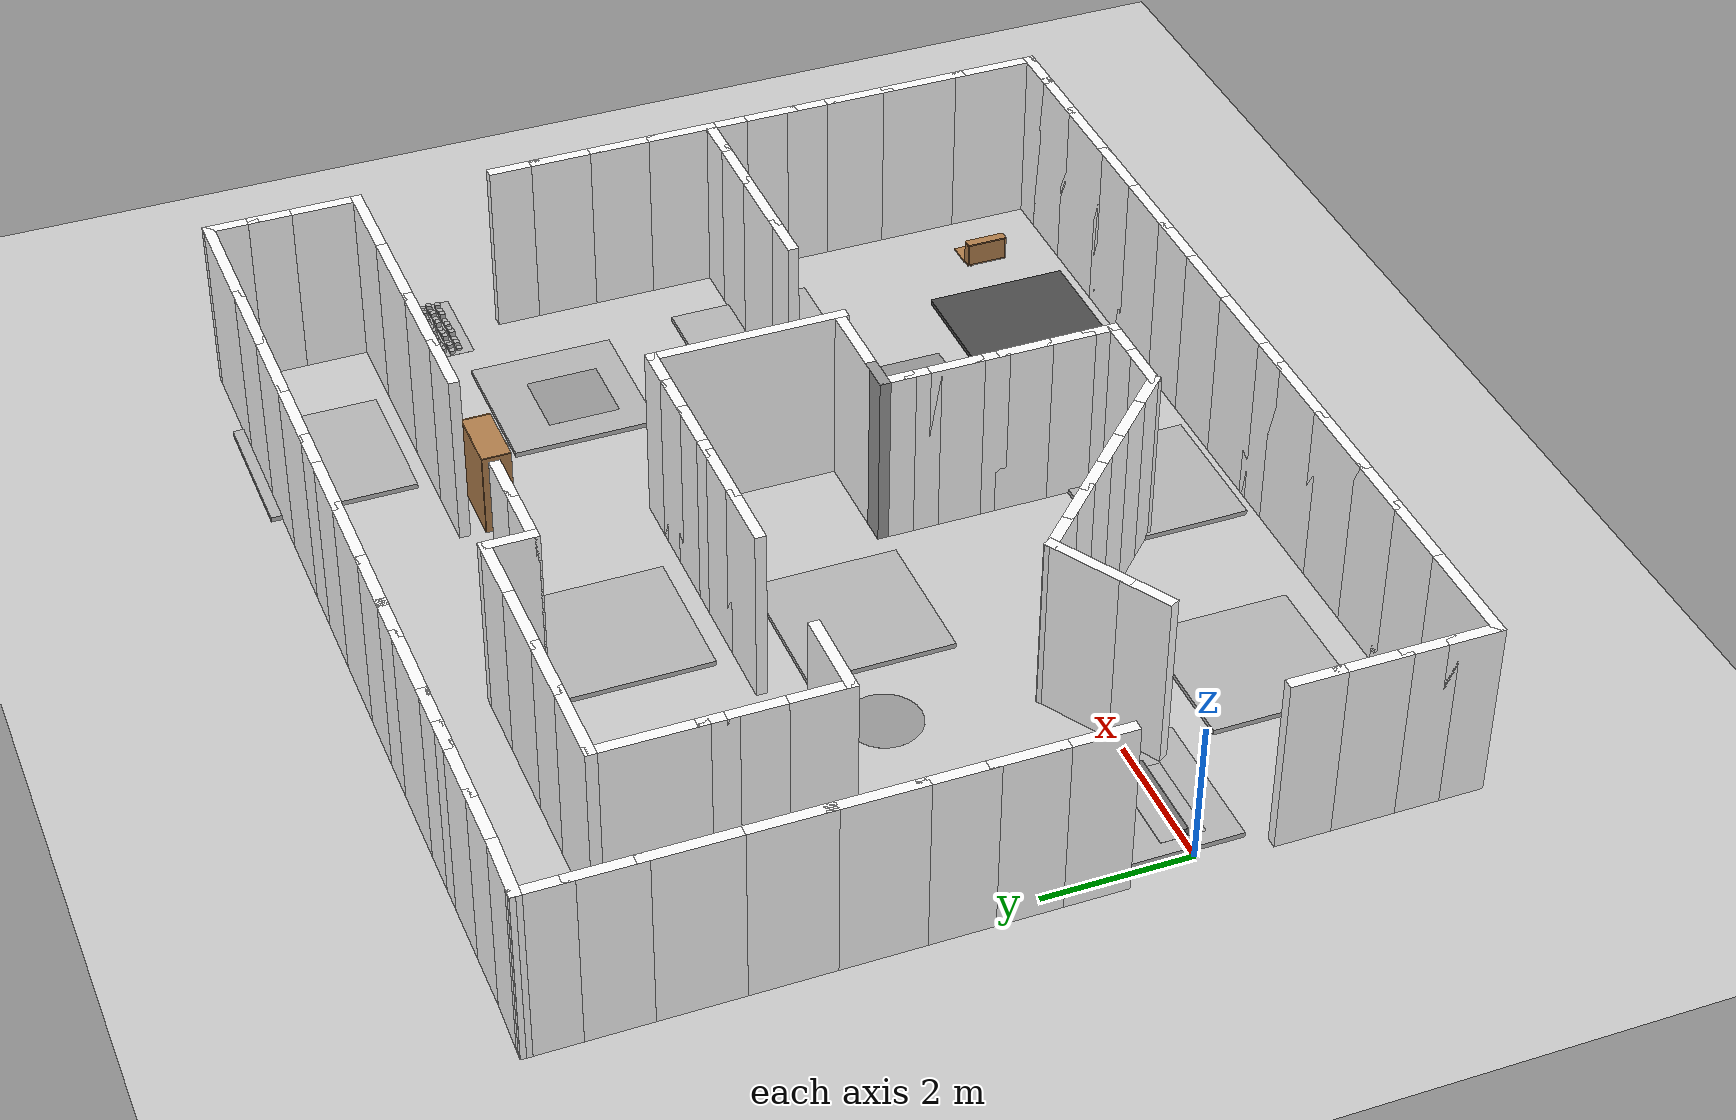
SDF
<sdf version="1.6">
 <world name="default">
  <light name="sun" type="directional">
   <pose>0 0 10 0 -0 0</pose>
   <diffuse>0.8 0.8 0.8 1</diffuse>
   <specular>0.1 0.1 0.1 1</specular>
   <attenuation>
    <range>1000</range>
    <constant>0.9</constant>
    <linear>0.01</linear>
    <quadratic>0.001</quadratic>
   </attenuation>
   <direction>-0.5 0.5 -1</direction>
  </light>
  <plugin name="ros_interface_plugin" filename="librotors_gazebo_ros_interface_plugin.so"/>
  <spherical_coordinates>
   <surface_model>EARTH_WGS84</surface_model>
   <latitude_deg>47.3667</latitude_deg>
   <longitude_deg>8.55</longitude_deg>
   <elevation>500</elevation>
   <heading_deg>0</heading_deg>
  </spherical_coordinates>
  <physics name="default_physics" default="0" type="ode">
   <ode>
    <solver>
     <type>quick</type>
     <iters>1000</iters>
     <sor>1.3</sor>
     <use_dynamic_moi_rescaling>0</use_dynamic_moi_rescaling>
    </solver>
    <constraints>
     <cfm>0</cfm>
     <erp>0.2</erp>
     <contact_max_correcting_vel>100</contact_max_correcting_vel>
     <contact_surface_layer>0.001</contact_surface_layer>
    </constraints>
   </ode>
   <max_step_size>0.01</max_step_size>
   <real_time_factor>1</real_time_factor>
   <real_time_update_rate>100</real_time_update_rate>
  </physics>
  <gravity>0 0 -9.8</gravity>
  <magnetic_field>6e-06 2.3e-05 -4.2e-05</magnetic_field>
  <atmosphere type="adiabatic"/>
  <scene><ambient>0.4 0.4 0.4 1</ambient><background>0.7 0.7 0.7 1</background><shadows>1</shadows></scene>
  <model name="texture1">
   <static>1</static>
   <link name="link">
    <collision name="collision"><geometry><box><size>2 2 0.1</size></box></geometry></collision>
    <visual name="visual">
     <cast_shadows>0</cast_shadows>
     <geometry><box><size>2 2 0.1</size></box></geometry>
     <material>
      <script>
       <uri>model://texture1/materials/scripts</uri>
       <uri>model://texture1/materials/textures</uri>
       <name>vrc/texture1</name>
      </script>
     </material>
    </visual>
   </link>
   <pose>1.10495 0.295237 0 0 -0 0</pose>
  </model>
  <model name="texture2">
   <static>1</static>
   <link name="link">
    <collision name="collision"><geometry><box><size>2 2 0.1</size></box></geometry></collision>
    <visual name="visual">
     <cast_shadows>0</cast_shadows>
     <geometry><box><size>2 2 0.1</size></box></geometry>
     <material>
      <script>
       <uri>model://texture2/materials/scripts</uri>
       <uri>model://texture2/materials/textures</uri>
       <name>vrc/texture2</name>
      </script>
     </material>
    </visual>
   </link>
   <pose>2.86208 -2.15151 0 0 -0 0</pose>
  </model>
  <model name="texture4">
   <static>1</static>
   <link name="link">
    <collision name="collision"><geometry><box><size>2 2 0.1</size></box></geometry></collision>
    <visual name="visual">
     <cast_shadows>0</cast_shadows>
     <geometry><box><size>2 2 0.1</size></box></geometry>
     <material>
      <script>
       <uri>model://texture4/materials/scripts</uri>
       <uri>model://texture4/materials/textures</uri>
       <name>vrc/texture4</name>
      </script>
     </material>
    </visual>
   </link>
   <pose>6.58941 -2.46684 0 0 -0 0</pose>
  </model>
  <model name="asphalt_plane_1">
   <static>1</static>
   <link name="link">
    <collision name="collision"><geometry><box><size>2 2 0.1</size></box></geometry></collision>
    <visual name="visual">
     <cast_shadows>0</cast_shadows>
     <geometry><box><size>2 2 0.1</size></box></geometry>
     <material>
      <script>
       <uri>model://texture3/materials/scripts</uri>
       <uri>model://texture3/materials/textures</uri>
       <name>vrc/asphalt</name>
      </script>
     </material>
    </visual>
   </link>
   <pose>10.5004 -2.44355 0 0 -0 0</pose>
  </model>
  <model name="texture1_0">
   <static>1</static>
   <link name="link">
    <collision name="collision"><geometry><box><size>2 2 0.1</size></box></geometry></collision>
    <visual name="visual">
     <cast_shadows>0</cast_shadows>
     <geometry><box><size>2 2 0.1</size></box></geometry>
     <material>
      <script>
       <uri>model://texture1/materials/scripts</uri>
       <uri>model://texture1/materials/textures</uri>
       <name>vrc/texture1</name>
      </script>
     </material>
    </visual>
   </link>
   <pose>8.52201 -0.164778 0 0 -0 0</pose>
  </model>
  <model name="texture2_0">
   <static>1</static>
   <link name="link">
    <collision name="collision"><geometry><box><size>2 2 0.1</size></box></geometry></collision>
    <visual name="visual">
     <cast_shadows>0</cast_shadows>
     <geometry><box><size>2 2 0.1</size></box></geometry>
     <material>
      <script>
       <uri>model://texture2/materials/scripts</uri>
       <uri>model://texture2/materials/textures</uri>
       <name>vrc/texture2</name>
      </script>
     </material>
    </visual>
   </link>
   <pose>11.4317 1.11566 0 0 -0 0</pose>
  </model>
  <model name="texture4_0">
   <static>1</static>
   <link name="link">
    <collision name="collision"><geometry><box><size>2 2 0.1</size></box></geometry></collision>
    <visual name="visual">
     <cast_shadows>0</cast_shadows>
     <geometry><box><size>2 2 0.1</size></box></geometry>
     <material>
      <script>
       <uri>model://texture4/materials/scripts</uri>
       <uri>model://texture4/materials/textures</uri>
       <name>vrc/texture4</name>
      </script>
     </material>
    </visual>
   </link>
   <pose>11.2423 4.1124 0 0 -0 0</pose>
  </model>
  <model name="texture1_1">
   <static>1</static>
   <link name="link">
    <collision name="collision"><geometry><box><size>2 2 0.1</size></box></geometry></collision>
    <visual name="visual">
     <cast_shadows>0</cast_shadows>
     <geometry><box><size>2 2 0.1</size></box></geometry>
     <material>
      <script>
       <uri>model://texture1/materials/scripts</uri>
       <uri>model://texture1/materials/textures</uri>
       <name>vrc/texture1</name>
      </script>
     </material>
    </visual>
   </link>
   <pose>5.50732 2.14153 0 0 -0 0</pose>
  </model>
  <model name="texture2_1">
   <static>1</static>
   <link name="link">
    <collision name="collision"><geometry><box><size>2 2 0.1</size></box></geometry></collision>
    <visual name="visual">
     <cast_shadows>0</cast_shadows>
     <geometry><box><size>2 2 0.1</size></box></geometry>
     <material>
      <script>
       <uri>model://texture2/materials/scripts</uri>
       <uri>model://texture2/materials/textures</uri>
       <name>vrc/texture2</name>
      </script>
     </material>
    </visual>
   </link>
   <pose>6.2809 5.0697 0 0 -0 0</pose>
  </model>
  <model name="texture4_1">
   <static>1</static>
   <link name="link">
    <collision name="collision"><geometry><box><size>2 2 0.1</size></box></geometry></collision>
    <visual name="visual">
     <cast_shadows>0</cast_shadows>
     <geometry><box><size>2 2 0.1</size></box></geometry>
     <material>
      <script>
       <uri>model://texture4/materials/scripts</uri>
       <uri>model://texture4/materials/textures</uri>
       <name>vrc/texture4</name>
      </script>
     </material>
    </visual>
   </link>
   <pose>3.34657 5.22733 0 0 -0 0</pose>
  </model>
  <model name="texture1_2">
   <static>1</static>
   <link name="link">
    <collision name="collision"><geometry><box><size>2 2 0.1</size></box></geometry></collision>
    <visual name="visual">
     <cast_shadows>0</cast_shadows>
     <geometry><box><size>2 2 0.1</size></box></geometry>
     <material>
      <script>
       <uri>model://texture1/materials/scripts</uri>
       <uri>model://texture1/materials/textures</uri>
       <name>vrc/texture1</name>
      </script>
     </material>
    </visual>
   </link>
   <pose>11.0808 7.52286 0 0 -0 0</pose>
  </model>
  <model name="asphalt_plane_2">
   <static>1</static>
   <link name="link">
    <collision name="collision"><geometry><box><size>2 2 0.1</size></box></geometry></collision>
    <visual name="visual">
     <cast_shadows>0</cast_shadows>
     <geometry><box><size>2 2 0.1</size></box></geometry>
     <material>
      <script>
       <uri>model://texture3/materials/scripts</uri>
       <uri>model://texture3/materials/textures</uri>
       <name>vrc/asphalt</name>
      </script>
     </material>
    </visual>
   </link>
   <pose>1.00288 5.06011 0 0 -0 0</pose>
  </model>
  <model name="obstacles">
   <pose>6.59109 2.33085 0 0 -0 0</pose>
   <link name="Wall_11">
    <collision name="Wall_11_Collision">
     <geometry><box><size>0.75 0.15 2.5</size></box></geometry>
     <pose>0 0 1.25 0 -0 0</pose>
    </collision>
    <visual name="Wall_11_Visual">
     <pose>0 0 1.25 0 -0 0</pose>
     <geometry><box><size>0.75 0.15 2.5</size></box></geometry>
     <material>
      <script><uri>file://media/materials/scripts/gazebo.material</uri><name>Gazebo/Texture1</name></script>
      <ambient>1 1 1 1</ambient>
     </material>
    </visual>
    <pose>-6.70688 -3.64234 0 0 0 -1.5708</pose>
   </link>
   <link name="Wall_12">
    <collision name="Wall_12_Collision">
     <geometry><box><size>1 0.15 2.5</size></box></geometry>
     <pose>0 0 1.25 0 -0 0</pose>
    </collision>
    <visual name="Wall_12_Visual">
     <pose>0 0 1.25 0 -0 0</pose>
     <geometry><box><size>1 0.15 2.5</size></box></geometry>
     <material>
      <script><uri>file://media/materials/scripts/gazebo.material</uri><name>Gazebo/Texture2</name></script>
      <ambient>1 1 1 1</ambient>
     </material>
    </visual>
    <pose>-6.70688 -4.36734 0 0 0 -1.5708</pose>
   </link>
   <link name="Wall_13">
    <collision name="Wall_13_Collision">
     <geometry><box><size>0.75 0.15 2.5</size></box></geometry>
     <pose>0 0 1.25 0 -0 0</pose>
    </collision>
    <visual name="Wall_13_Visual">
     <pose>0 0 1.25 0 -0 0</pose>
     <geometry><box><size>0.75 0.15 2.5</size></box></geometry>
     <material>
      <script><uri>file://media/materials/scripts/gazebo.material</uri><name>Gazebo/Texture3</name></script>
      <ambient>1 1 1 1</ambient>
     </material>
    </visual>
    <pose>-6.70688 -5.09234 0 0 0 -1.5708</pose>
   </link>
   <link name="Wall_14">
    <collision name="Wall_14_Collision">
     <geometry><box><size>0.75 0.15 2.5</size></box></geometry>
     <pose>0 0 1.25 0 -0 0</pose>
    </collision>
    <visual name="Wall_14_Visual">
     <pose>0 0 1.25 0 -0 0</pose>
     <geometry><box><size>0.75 0.15 2.5</size></box></geometry>
     <material>
      <script><uri>file://media/materials/scripts/gazebo.material</uri><name>Gazebo/Texture4</name></script>
      <ambient>1 1 1 1</ambient>
     </material>
    </visual>
    <pose>-6.70688 -5.69234 0 0 0 -1.5708</pose>
   </link>
   <link name="Wall_15">
    <collision name="Wall_15_Collision">
     <geometry><box><size>1.5 0.15 2.5</size></box></geometry>
     <pose>0 0 1.25 0 -0 0</pose>
    </collision>
    <visual name="Wall_15_Visual">
     <pose>0 0 1.25 0 -0 0</pose>
     <geometry><box><size>1.5 0.15 2.5</size></box></geometry>
     <material>
      <script><uri>file://media/materials/scripts/gazebo.material</uri><name>Gazebo/Texture5</name></script>
      <ambient>1 1 1 1</ambient>
     </material>
    </visual>
    <pose>-6.03188 -5.99234 0 0 -0 0</pose>
   </link>
   <link name="Wall_16">
    <collision name="Wall_16_Collision">
     <geometry><box><size>1.25 0.15 2.5</size></box></geometry>
     <pose>0 0 1.25 0 -0 0</pose>
    </collision>
    <visual name="Wall_16_Visual">
     <pose>0 0 1.25 0 -0 0</pose>
     <geometry><box><size>1.25 0.15 2.5</size></box></geometry>
     <material>
      <script><uri>file://media/materials/scripts/gazebo.material</uri><name>Gazebo/Texture6</name></script>
      <ambient>1 1 1 1</ambient>
     </material>
    </visual>
    <pose>-4.80688 -5.99234 0 0 -0 0</pose>
   </link>
   <link name="Wall_17">
    <collision name="Wall_17_Collision">
     <geometry><box><size>1 0.15 2.5</size></box></geometry>
     <pose>0 0 1.25 0 -0 0</pose>
    </collision>
    <visual name="Wall_17_Visual">
     <pose>0 0 1.25 0 -0 0</pose>
     <geometry><box><size>1 0.15 2.5</size></box></geometry>
     <material>
      <script><uri>file://media/materials/scripts/gazebo.material</uri><name>Gazebo/Texture7</name></script>
      <ambient>1 1 1 1</ambient>
     </material>
    </visual>
    <pose>-3.83188 -5.99234 0 0 -0 0</pose>
   </link>
   <link name="Wall_18">
    <collision name="Wall_18_Collision">
     <geometry><box><size>1.25 0.15 2.5</size></box></geometry>
     <pose>0 0 1.25 0 -0 0</pose>
    </collision>
    <visual name="Wall_18_Visual">
     <pose>0 0 1.25 0 -0 0</pose>
     <geometry><box><size>1.25 0.15 2.5</size></box></geometry>
     <material>
      <script><uri>file://media/materials/scripts/gazebo.material</uri><name>Gazebo/Texture8</name></script>
      <ambient>1 1 1 1</ambient>
     </material>
    </visual>
    <pose>-2.85688 -5.99234 0 0 -0 0</pose>
   </link>
   <link name="Wall_19">
    <collision name="Wall_19_Collision">
     <geometry><box><size>1.25 0.15 2.5</size></box></geometry>
     <pose>0 0 1.25 0 -0 0</pose>
    </collision>
    <visual name="Wall_19_Visual">
     <pose>0 0 1.25 0 -0 0</pose>
     <geometry><box><size>1.25 0.15 2.5</size></box></geometry>
     <material>
      <script><uri>file://media/materials/scripts/gazebo.material</uri><name>Gazebo/Texture9</name></script>
      <ambient>1 1 1 1</ambient>
     </material>
    </visual>
    <pose>-1.75688 -5.99234 0 0 -0 0</pose>
   </link>
   <link name="Wall_2">
    <collision name="Wall_2_Collision">
     <geometry><box><size>0.75 0.15 2.5</size></box></geometry>
     <pose>0 0 1.25 0 -0 0</pose>
    </collision>
    <visual name="Wall_2_Visual">
     <pose>0 0 1.25 0 -0 0</pose>
     <geometry><box><size>0.75 0.15 2.5</size></box></geometry>
     <material>
      <script><uri>file://media/materials/scripts/gazebo.material</uri><name>Gazebo/Texture10</name></script>
      <ambient>1 1 1 1</ambient>
     </material>
    </visual>
    <pose>-6.72699 5.69035 0 0 0 -1.5708</pose>
   </link>
   <link name="Wall_20">
    <collision name="Wall_20_Collision">
     <geometry><box><size>0.75 0.15 2.5</size></box></geometry>
     <pose>0 0 1.25 0 -0 0</pose>
    </collision>
    <visual name="Wall_20_Visual">
     <pose>0 0 1.25 0 -0 0</pose>
     <geometry><box><size>0.75 0.15 2.5</size></box></geometry>
     <material>
      <script><uri>file://media/materials/scripts/gazebo.material</uri><name>Gazebo/Texture11</name></script>
      <ambient>1 1 1 1</ambient>
     </material>
    </visual>
    <pose>-0.90688 -5.99234 0 0 -0 0</pose>
   </link>
   <link name="Wall_202">
    <collision name="Wall_202_Collision">
     <geometry><box><size>1.25 0.15 2.5</size></box></geometry>
     <pose>0 0 1.25 0 -0 0</pose>
    </collision>
    <visual name="Wall_202_Visual">
     <pose>0 0 1.25 0 -0 0</pose>
     <geometry><box><size>1.25 0.15 2.5</size></box></geometry>
     <material>
      <script><uri>file://media/materials/scripts/gazebo.material</uri><name>Gazebo/Texture12</name></script>
      <ambient>1 1 1 1</ambient>
     </material>
    </visual>
    <pose>6.17899 3.91866 0 0 -0 3.14159</pose>
   </link>
   <link name="Wall_203">
    <collision name="Wall_203_Collision">
     <geometry><box><size>1.5 0.15 2.5</size></box></geometry>
     <pose>0 0 1.25 0 -0 0</pose>
    </collision>
    <visual name="Wall_203_Visual">
     <pose>0 0 1.25 0 -0 0</pose>
     <geometry><box><size>1.5 0.15 2.5</size></box></geometry>
     <material>
      <script><uri>file://media/materials/scripts/gazebo.material</uri><name>Gazebo/Texture13</name></script>
      <ambient>1 1 1 1</ambient>
     </material>
    </visual>
    <pose>4.95399 3.91866 0 0 -0 3.14159</pose>
   </link>
   <link name="Wall_204">
    <collision name="Wall_204_Collision">
     <geometry><box><size>1.25 0.15 2.5</size></box></geometry>
     <pose>0 0 1.25 0 -0 0</pose>
    </collision>
    <visual name="Wall_204_Visual">
     <pose>0 0 1.25 0 -0 0</pose>
     <geometry><box><size>1.25 0.15 2.5</size></box></geometry>
     <material>
      <script><uri>file://media/materials/scripts/gazebo.material</uri><name>Gazebo/Texture14</name></script>
      <ambient>1 1 1 1</ambient>
     </material>
    </visual>
    <pose>3.72899 3.91866 0 0 -0 3.14159</pose>
   </link>
   <link name="Wall_205">
    <collision name="Wall_205_Collision">
     <geometry><box><size>1 0.15 2.5</size></box></geometry>
     <pose>0 0 1.25 0 -0 0</pose>
    </collision>
    <visual name="Wall_205_Visual">
     <pose>0 0 1.25 0 -0 0</pose>
     <geometry><box><size>1 0.15 2.5</size></box></geometry>
     <material>
      <script><uri>file://media/materials/scripts/gazebo.material</uri><name>Gazebo/Texture15</name></script>
      <ambient>1 1 1 1</ambient>
     </material>
    </visual>
    <pose>2.75399 3.91866 0 0 -0 3.14159</pose>
   </link>
   <link name="Wall_207">
    <collision name="Wall_207_Collision">
     <geometry><box><size>0.75 0.15 2.5</size></box></geometry>
     <pose>0 0 1.25 0 -0 0</pose>
    </collision>
    <visual name="Wall_207_Visual">
     <pose>0 0 1.25 0 -0 0</pose>
     <geometry><box><size>0.75 0.15 2.5</size></box></geometry>
     <material>
      <script><uri>file://media/materials/scripts/gazebo.material</uri><name>Gazebo/Texture16</name></script>
      <ambient>1 1 1 1</ambient>
     </material>
    </visual>
    <pose>0.155851 3.92543 0 0 -0 3.14159</pose>
   </link>
   <link name="Wall_208">
    <collision name="Wall_208_Collision">
     <geometry><box><size>1 0.15 2.5</size></box></geometry>
     <pose>0 0 1.25 0 -0 0</pose>
    </collision>
    <visual name="Wall_208_Visual">
     <pose>0 0 1.25 0 -0 0</pose>
     <geometry><box><size>1 0.15 2.5</size></box></geometry>
     <material>
      <script><uri>file://media/materials/scripts/gazebo.material</uri><name>Gazebo/Texture17</name></script>
      <ambient>1 1 1 1</ambient>
     </material>
    </visual>
    <pose>-0.569149 3.92543 0 0 -0 3.14159</pose>
   </link>
   <link name="Wall_209">
    <collision name="Wall_209_Collision">
     <geometry><box><size>0.75 0.15 2.5</size></box></geometry>
     <pose>0 0 1.25 0 -0 0</pose>
    </collision>
    <visual name="Wall_209_Visual">
     <pose>0 0 1.25 0 -0 0</pose>
     <geometry><box><size>0.75 0.15 2.5</size></box></geometry>
     <material>
      <script><uri>file://media/materials/scripts/gazebo.material</uri><name>Gazebo/Texture18</name></script>
      <ambient>1 1 1 1</ambient>
     </material>
    </visual>
    <pose>-0.994149 4.22543 0 0 -0 1.5708</pose>
   </link>
   <link name="Wall_21">
    <collision name="Wall_21_Collision">
     <geometry><box><size>1.25 0.15 2.5</size></box></geometry>
     <pose>0 0 1.25 0 -0 0</pose>
    </collision>
    <visual name="Wall_21_Visual">
     <pose>0 0 1.25 0 -0 0</pose>
     <geometry><box><size>1.25 0.15 2.5</size></box></geometry>
     <material>
      <script><uri>file://media/materials/scripts/gazebo.material</uri><name>Gazebo/Texture19</name></script>
      <ambient>1 1 1 1</ambient>
     </material>
    </visual>
    <pose>-0.05688 -5.99234 0 0 -0 0</pose>
   </link>
   <link name="Wall_210">
    <collision name="Wall_210_Collision">
     <geometry><box><size>1 0.15 2.5</size></box></geometry>
     <pose>0 0 1.25 0 -0 0</pose>
    </collision>
    <visual name="Wall_210_Visual">
     <pose>0 0 1.25 0 -0 0</pose>
     <geometry><box><size>1 0.15 2.5</size></box></geometry>
     <material>
      <script><uri>file://media/materials/scripts/gazebo.material</uri><name>Gazebo/Texture20</name></script>
      <ambient>1 1 1 1</ambient>
     </material>
    </visual>
    <pose>-1.41915 4.52543 0 0 -0 3.14159</pose>
   </link>
   <link name="Wall_211">
    <collision name="Wall_211_Collision">
     <geometry><box><size>1.25 0.15 2.5</size></box></geometry>
     <pose>0 0 1.25 0 -0 0</pose>
    </collision>
    <visual name="Wall_211_Visual">
     <pose>0 0 1.25 0 -0 0</pose>
     <geometry><box><size>1.25 0.15 2.5</size></box></geometry>
     <material>
      <script><uri>file://media/materials/scripts/gazebo.material</uri><name>Gazebo/Texture21</name></script>
      <ambient>1 1 1 1</ambient>
     </material>
    </visual>
    <pose>-2.39415 4.52543 0 0 -0 3.14159</pose>
   </link>
   <link name="Wall_212">
    <collision name="Wall_212_Collision">
     <geometry><box><size>1 0.15 2.5</size></box></geometry>
     <pose>0 0 1.25 0 -0 0</pose>
    </collision>
    <visual name="Wall_212_Visual">
     <pose>0 0 1.25 0 -0 0</pose>
     <geometry><box><size>1 0.15 2.5</size></box></geometry>
     <material>
      <script><uri>file://media/materials/scripts/gazebo.material</uri><name>Gazebo/Texture22</name></script>
      <ambient>1 1 1 1</ambient>
     </material>
    </visual>
    <pose>-3.36915 4.52543 0 0 -0 3.14159</pose>
   </link>
   <link name="Wall_213">
    <collision name="Wall_213_Collision">
     <geometry><box><size>1.25 0.15 2.5</size></box></geometry>
     <pose>0 0 1.25 0 -0 0</pose>
    </collision>
    <visual name="Wall_213_Visual">
     <pose>0 0 1.25 0 -0 0</pose>
     <geometry><box><size>1.25 0.15 2.5</size></box></geometry>
     <material>
      <script><uri>file://media/materials/scripts/gazebo.material</uri><name>Gazebo/Texture23</name></script>
      <ambient>1 1 1 1</ambient>
     </material>
    </visual>
    <pose>-4.34415 4.52543 0 0 -0 3.14159</pose>
   </link>
   <link name="Wall_214">
    <collision name="Wall_214_Collision">
     <geometry><box><size>1.5 0.15 2.5</size></box></geometry>
     <pose>0 0 1.25 0 -0 0</pose>
    </collision>
    <visual name="Wall_214_Visual">
     <pose>0 0 1.25 0 -0 0</pose>
     <geometry><box><size>1.5 0.15 2.5</size></box></geometry>
     <material>
      <script><uri>file://media/materials/scripts/gazebo.material</uri><name>Gazebo/Texture24</name></script>
      <ambient>1 1 1 1</ambient>
     </material>
    </visual>
    <pose>-4.89415 3.85043 0 0 0 -1.5708</pose>
   </link>
   <link name="Wall_215">
    <collision name="Wall_215_Collision">
     <geometry><box><size>0.5 0.15 2.5</size></box></geometry>
     <pose>0 0 1.25 0 -0 0</pose>
    </collision>
    <visual name="Wall_215_Visual">
     <pose>0 0 1.25 0 -0 0</pose>
     <geometry><box><size>0.5 0.15 2.5</size></box></geometry>
     <material>
      <script><uri>file://media/materials/scripts/gazebo.material</uri><name>Gazebo/Texture25</name></script>
      <ambient>1 1 1 1</ambient>
     </material>
    </visual>
    <pose>-4.89415 3.00043 0 0 0 -1.5708</pose>
   </link>
   <link name="Wall_216">
    <collision name="Wall_216_Collision">
     <geometry><box><size>0.75 0.15 2.5</size></box></geometry>
     <pose>0 0 1.25 0 -0 0</pose>
    </collision>
    <visual name="Wall_216_Visual">
     <pose>0 0 1.25 0 -0 0</pose>
     <geometry><box><size>0.75 0.15 2.5</size></box></geometry>
     <material>
      <script><uri>file://media/materials/scripts/gazebo.material</uri><name>Gazebo/Texture26</name></script>
      <ambient>1 1 1 1</ambient>
     </material>
    </visual>
    <pose>-4.89415 2.52543 0 0 0 -1.5708</pose>
   </link>
   <link name="Wall_217">
    <collision name="Wall_217_Collision">
     <geometry><box><size>1 0.15 2.5</size></box></geometry>
     <pose>0 0 1.25 0 -0 0</pose>
    </collision>
    <visual name="Wall_217_Visual">
     <pose>0 0 1.25 0 -0 0</pose>
     <geometry><box><size>1 0.15 2.5</size></box></geometry>
     <material>
      <script><uri>file://media/materials/scripts/gazebo.material</uri><name>Gazebo/Texture27</name></script>
      <ambient>1 1 1 1</ambient>
     </material>
    </visual>
    <pose>-4.89415 1.80043 0 0 0 -1.5708</pose>
   </link>
   <link name="Wall_218">
    <collision name="Wall_218_Collision">
     <geometry><box><size>1.25 0.15 2.5</size></box></geometry>
     <pose>0 0 1.25 0 -0 0</pose>
    </collision>
    <visual name="Wall_218_Visual">
     <pose>0 0 1.25 0 -0 0</pose>
     <geometry><box><size>1.25 0.15 2.5</size></box></geometry>
     <material>
      <script><uri>file://media/materials/scripts/gazebo.material</uri><name>Gazebo/Texture28</name></script>
      <ambient>1 1 1 1</ambient>
     </material>
    </visual>
    <pose>-4.34415 1.37543 0 0 -0 0</pose>
   </link>
   <link name="Wall_22">
    <collision name="Wall_22_Collision">
     <geometry><box><size>1 0.15 2.5</size></box></geometry>
     <pose>0 0 1.25 0 -0 0</pose>
    </collision>
    <visual name="Wall_22_Visual">
     <pose>0 0 1.25 0 -0 0</pose>
     <geometry><box><size>1 0.15 2.5</size></box></geometry>
     <material>
      <script><uri>file://media/materials/scripts/gazebo.material</uri><name>Gazebo/Texture29</name></script>
      <ambient>1 1 1 1</ambient>
     </material>
    </visual>
    <pose>0.91812 -5.99234 0 0 -0 0</pose>
   </link>
   <link name="Wall_220">
    <collision name="Wall_220_Collision">
     <geometry><box><size>1 0.15 2.5</size></box></geometry>
     <pose>0 0 1.25 0 -0 0</pose>
    </collision>
    <visual name="Wall_220_Visual">
     <pose>0 0 1.25 0 -0 0</pose>
     <geometry><box><size>1 0.15 2.5</size></box></geometry>
     <material>
      <script><uri>file://media/materials/scripts/gazebo.material</uri><name>Gazebo/Texture30</name></script>
      <ambient>1 1 1 1</ambient>
     </material>
    </visual>
    <pose>-1.54786 1.4042 0 0 -0 0</pose>
   </link>
   <link name="Wall_221">
    <collision name="Wall_221_Collision">
     <geometry><box><size>1 0.15 2.5</size></box></geometry>
     <pose>0 0 1.25 0 -0 0</pose>
    </collision>
    <visual name="Wall_221_Visual">
     <pose>0 0 1.25 0 -0 0</pose>
     <geometry><box><size>1 0.15 2.5</size></box></geometry>
     <material>
      <script><uri>file://media/materials/scripts/gazebo.material</uri><name>Gazebo/Texture31</name></script>
      <ambient>1 1 1 1</ambient>
     </material>
    </visual>
    <pose>-0.697863 1.4042 0 0 -0 0</pose>
   </link>
   <link name="Wall_222">
    <collision name="Wall_222_Collision">
     <geometry><box><size>0.5 0.15 2.5</size></box></geometry>
     <pose>0 0 1.25 0 -0 0</pose>
    </collision>
    <visual name="Wall_222_Visual">
     <pose>0 0 1.25 0 -0 0</pose>
     <geometry><box><size>0.5 0.15 2.5</size></box></geometry>
     <material>
      <script><uri>file://media/materials/scripts/gazebo.material</uri><name>Gazebo/Texture32</name></script>
      <ambient>1 1 1 1</ambient>
     </material>
    </visual>
    <pose>-0.097863 1.4042 0 0 -0 0</pose>
   </link>
   <link name="Wall_223">
    <collision name="Wall_223_Collision">
     <geometry><box><size>0.75 0.15 2.5</size></box></geometry>
     <pose>0 0 1.25 0 -0 0</pose>
    </collision>
    <visual name="Wall_223_Visual">
     <pose>0 0 1.25 0 -0 0</pose>
     <geometry><box><size>0.75 0.15 2.5</size></box></geometry>
     <material>
      <script><uri>file://media/materials/scripts/gazebo.material</uri><name>Gazebo/Texture33</name></script>
      <ambient>1 1 1 1</ambient>
     </material>
    </visual>
    <pose>0.377137 1.4042 0 0 -0 0</pose>
   </link>
   <link name="Wall_224">
    <collision name="Wall_224_Collision">
     <geometry><box><size>0.75 0.15 2.5</size></box></geometry>
     <pose>0 0 1.25 0 -0 0</pose>
    </collision>
    <visual name="Wall_224_Visual">
     <pose>0 0 1.25 0 -0 0</pose>
     <geometry><box><size>0.75 0.15 2.5</size></box></geometry>
     <material>
      <script><uri>file://media/materials/scripts/gazebo.material</uri><name>Gazebo/Texture34</name></script>
      <ambient>1 1 1 1</ambient>
     </material>
    </visual>
    <pose>0.977137 1.4042 0 0 -0 0</pose>
   </link>
   <link name="Wall_225">
    <collision name="Wall_225_Collision">
     <geometry><box><size>0.75 0.15 2.5</size></box></geometry>
     <pose>0 0 1.25 0 -0 0</pose>
    </collision>
    <visual name="Wall_225_Visual">
     <pose>0 0 1.25 0 -0 0</pose>
     <geometry><box><size>0.75 0.15 2.5</size></box></geometry>
     <material>
      <script><uri>file://media/materials/scripts/gazebo.material</uri><name>Gazebo/Texture35</name></script>
      <ambient>1 1 1 1</ambient>
     </material>
    </visual>
    <pose>1.57714 1.4042 0 0 -0 0</pose>
   </link>
   <link name="Wall_226">
    <collision name="Wall_226_Collision">
     <geometry><box><size>2.75 0.15 2.5</size></box></geometry>
     <pose>0 0 1.25 0 -0 0</pose>
    </collision>
    <visual name="Wall_226_Visual">
     <pose>0 0 1.25 0 -0 0</pose>
     <geometry><box><size>2.75 0.15 2.5</size></box></geometry>
     <material>
      <script><uri>file://media/materials/scripts/gazebo.material</uri><name>Gazebo/Texture36</name></script>
      <ambient>1 1 1 1</ambient>
     </material>
    </visual>
    <pose>1.87714 0.104195 0 0 0 -1.5708</pose>
   </link>
   <link name="Wall_228">
    <collision name="Wall_228_Collision">
     <geometry><box><size>0.75 0.15 2.5</size></box></geometry>
     <pose>0 0 1.25 0 -0 0</pose>
    </collision>
    <visual name="Wall_228_Visual">
     <pose>0 0 1.25 0 -0 0</pose>
     <geometry><box><size>0.75 0.15 2.5</size></box></geometry>
     <material>
      <script><uri>file://media/materials/scripts/gazebo.material</uri><name>Gazebo/Texture37</name></script>
      <ambient>1 1 1 1</ambient>
     </material>
    </visual>
    <pose>0.031047 -4.34997 0 0 -0 3.14159</pose>
   </link>
   <link name="Wall_229">
    <collision name="Wall_229_Collision">
     <geometry><box><size>0.75 0.15 2.5</size></box></geometry>
     <pose>0 0 1.25 0 -0 0</pose>
    </collision>
    <visual name="Wall_229_Visual">
     <pose>0 0 1.25 0 -0 0</pose>
     <geometry><box><size>0.75 0.15 2.5</size></box></geometry>
     <material>
      <script><uri>file://media/materials/scripts/gazebo.material</uri><name>Gazebo/Texture38</name></script>
      <ambient>1 1 1 1</ambient>
     </material>
    </visual>
    <pose>-0.568953 -4.34997 0 0 -0 3.14159</pose>
   </link>
   <link name="Wall_23">
    <collision name="Wall_23_Collision">
     <geometry><box><size>1 0.15 2.5</size></box></geometry>
     <pose>0 0 1.25 0 -0 0</pose>
    </collision>
    <visual name="Wall_23_Visual">
     <pose>0 0 1.25 0 -0 0</pose>
     <geometry><box><size>1 0.15 2.5</size></box></geometry>
     <material>
      <script><uri>file://media/materials/scripts/gazebo.material</uri><name>Gazebo/Texture39</name></script>
      <ambient>1 1 1 1</ambient>
     </material>
    </visual>
    <pose>1.76812 -5.99234 0 0 -0 0</pose>
   </link>
   <link name="Wall_233">
    <collision name="Wall_233_Collision">
     <geometry><box><size>0.75 0.15 2.5</size></box></geometry>
     <pose>0 0 1.25 0 -0 0</pose>
    </collision>
    <visual name="Wall_233_Visual">
     <pose>0 0 1.25 0 -0 0</pose>
     <geometry><box><size>0.75 0.15 2.5</size></box></geometry>
     <material>
      <script><uri>file://media/materials/scripts/gazebo.material</uri><name>Gazebo/Texture40</name></script>
      <ambient>1 1 1 1</ambient>
     </material>
    </visual>
    <pose>-1.08109 -4.13783 0 0 -0 2.35619</pose>
   </link>
   <link name="Wall_234">
    <collision name="Wall_234_Collision">
     <geometry><box><size>0.75 0.15 2.5</size></box></geometry>
     <pose>0 0 1.25 0 -0 0</pose>
    </collision>
    <visual name="Wall_234_Visual">
     <pose>0 0 1.25 0 -0 0</pose>
     <geometry><box><size>0.75 0.15 2.5</size></box></geometry>
     <material>
      <script><uri>file://media/materials/scripts/gazebo.material</uri><name>Gazebo/Texture41</name></script>
      <ambient>1 1 1 1</ambient>
     </material>
    </visual>
    <pose>-1.50535 -3.71357 0 0 -0 2.35619</pose>
   </link>
   <link name="Wall_235">
    <collision name="Wall_235_Collision">
     <geometry><box><size>0.75 0.15 2.5</size></box></geometry>
     <pose>0 0 1.25 0 -0 0</pose>
    </collision>
    <visual name="Wall_235_Visual">
     <pose>0 0 1.25 0 -0 0</pose>
     <geometry><box><size>0.75 0.15 2.5</size></box></geometry>
     <material>
      <script><uri>file://media/materials/scripts/gazebo.material</uri><name>Gazebo/Texture42</name></script>
      <ambient>1 1 1 1</ambient>
     </material>
    </visual>
    <pose>-1.92961 -3.28931 0 0 -0 2.35619</pose>
   </link>
   <link name="Wall_236">
    <collision name="Wall_236_Collision">
     <geometry><box><size>0.75 0.15 2.5</size></box></geometry>
     <pose>0 0 1.25 0 -0 0</pose>
    </collision>
    <visual name="Wall_236_Visual">
     <pose>0 0 1.25 0 -0 0</pose>
     <geometry><box><size>0.75 0.15 2.5</size></box></geometry>
     <material>
      <script><uri>file://media/materials/scripts/gazebo.material</uri><name>Gazebo/Texture43</name></script>
      <ambient>1 1 1 1</ambient>
     </material>
    </visual>
    <pose>-2.35388 -2.86504 0 0 -0 2.35619</pose>
   </link>
   <link name="Wall_237">
    <collision name="Wall_237_Collision">
     <geometry><box><size>0.75 0.15 2.5</size></box></geometry>
     <pose>0 0 1.25 0 -0 0</pose>
    </collision>
    <visual name="Wall_237_Visual">
     <pose>0 0 1.25 0 -0 0</pose>
     <geometry><box><size>0.75 0.15 2.5</size></box></geometry>
     <material>
      <script><uri>file://media/materials/scripts/gazebo.material</uri><name>Gazebo/Texture1</name></script>
      <ambient>1 1 1 1</ambient>
     </material>
    </visual>
    <pose>-2.77814 -2.44078 0 0 -0 2.35619</pose>
   </link>
   <link name="Wall_238">
    <collision name="Wall_238_Collision">
     <geometry><box><size>0.75 0.15 2.5</size></box></geometry>
     <pose>0 0 1.25 0 -0 0</pose>
    </collision>
    <visual name="Wall_238_Visual">
     <pose>0 0 1.25 0 -0 0</pose>
     <geometry><box><size>0.75 0.15 2.5</size></box></geometry>
     <material>
      <script><uri>file://media/materials/scripts/gazebo.material</uri><name>Gazebo/Texture2</name></script>
      <ambient>1 1 1 1</ambient>
     </material>
    </visual>
    <pose>-3.20241 -2.01651 0 0 -0 2.35619</pose>
   </link>
   <link name="Wall_239">
    <collision name="Wall_239_Collision">
     <geometry><box><size>1.25 0.15 2.5</size></box></geometry>
     <pose>0 0 1.25 0 -0 0</pose>
    </collision>
    <visual name="Wall_239_Visual">
     <pose>0 0 1.25 0 -0 0</pose>
     <geometry><box><size>1.25 0.15 2.5</size></box></geometry>
     <material>
      <script><uri>file://media/materials/scripts/gazebo.material</uri><name>Gazebo/Texture3</name></script>
      <ambient>1 1 1 1</ambient>
     </material>
    </visual>
    <pose>-3.89085 -2.07938 0 0 0 -2.61799</pose>
   </link>
   <link name="Wall_24">
    <collision name="Wall_24_Collision">
     <geometry><box><size>1.25 0.15 2.5</size></box></geometry>
     <pose>0 0 1.25 0 -0 0</pose>
    </collision>
    <visual name="Wall_24_Visual">
     <pose>0 0 1.25 0 -0 0</pose>
     <geometry><box><size>1.25 0.15 2.5</size></box></geometry>
     <material>
      <script><uri>file://media/materials/scripts/gazebo.material</uri><name>Gazebo/Texture4</name></script>
      <ambient>1 1 1 1</ambient>
     </material>
    </visual>
    <pose>2.74312 -5.99234 0 0 -0 0</pose>
   </link>
   <link name="Wall_240">
    <collision name="Wall_240_Collision">
     <geometry><box><size>0.75 0.15 2.5</size></box></geometry>
     <pose>0 0 1.25 0 -0 0</pose>
    </collision>
    <visual name="Wall_240_Visual">
     <pose>0 0 1.25 0 -0 0</pose>
     <geometry><box><size>0.75 0.15 2.5</size></box></geometry>
     <material>
      <script><uri>file://media/materials/scripts/gazebo.material</uri><name>Gazebo/Texture5</name></script>
      <ambient>1 1 1 1</ambient>
     </material>
    </visual>
    <pose>-4.62697 -2.50438 0 0 0 -2.61799</pose>
   </link>
   <link name="Wall_25">
    <collision name="Wall_25_Collision">
     <geometry><box><size>1 0.15 2.5</size></box></geometry>
     <pose>0 0 1.25 0 -0 0</pose>
    </collision>
    <visual name="Wall_25_Visual">
     <pose>0 0 1.25 0 -0 0</pose>
     <geometry><box><size>1 0.15 2.5</size></box></geometry>
     <material>
      <script><uri>file://media/materials/scripts/gazebo.material</uri><name>Gazebo/Texture6</name></script>
      <ambient>1 1 1 1</ambient>
     </material>
    </visual>
    <pose>3.71812 -5.99234 0 0 -0 0</pose>
   </link>
   <link name="Wall_26">
    <collision name="Wall_26_Collision">
     <geometry><box><size>1.25 0.15 2.5</size></box></geometry>
     <pose>0 0 1.25 0 -0 0</pose>
    </collision>
    <visual name="Wall_26_Visual">
     <pose>0 0 1.25 0 -0 0</pose>
     <geometry><box><size>1.25 0.15 2.5</size></box></geometry>
     <material>
      <script><uri>file://media/materials/scripts/gazebo.material</uri><name>Gazebo/Texture7</name></script>
      <ambient>1 1 1 1</ambient>
     </material>
    </visual>
    <pose>4.69312 -5.99234 0 0 -0 0</pose>
   </link>
   <link name="Wall_27">
    <collision name="Wall_27_Collision">
     <geometry><box><size>1 0.15 2.5</size></box></geometry>
     <pose>0 0 1.25 0 -0 0</pose>
    </collision>
    <visual name="Wall_27_Visual">
     <pose>0 0 1.25 0 -0 0</pose>
     <geometry><box><size>1 0.15 2.5</size></box></geometry>
     <material>
      <script><uri>file://media/materials/scripts/gazebo.material</uri><name>Gazebo/Texture8</name></script>
      <ambient>1 1 1 1</ambient>
     </material>
    </visual>
    <pose>5.66812 -5.99234 0 0 -0 0</pose>
   </link>
   <link name="Wall_28">
    <collision name="Wall_28_Collision">
     <geometry><box><size>0.75 0.15 2.5</size></box></geometry>
     <pose>0 0 1.25 0 -0 0</pose>
    </collision>
    <visual name="Wall_28_Visual">
     <pose>0 0 1.25 0 -0 0</pose>
     <geometry><box><size>0.75 0.15 2.5</size></box></geometry>
     <material>
      <script><uri>file://media/materials/scripts/gazebo.material</uri><name>Gazebo/Texture9</name></script>
      <ambient>1 1 1 1</ambient>
     </material>
    </visual>
    <pose>6.39312 -5.99234 0 0 -0 0</pose>
   </link>
   <link name="Wall_29">
    <collision name="Wall_29_Collision">
     <geometry><box><size>1.25 0.15 2.5</size></box></geometry>
     <pose>0 0 1.25 0 -0 0</pose>
    </collision>
    <visual name="Wall_29_Visual">
     <pose>0 0 1.25 0 -0 0</pose>
     <geometry><box><size>1.25 0.15 2.5</size></box></geometry>
     <material>
      <script><uri>file://media/materials/scripts/gazebo.material</uri><name>Gazebo/Texture10</name></script>
      <ambient>1 1 1 1</ambient>
     </material>
    </visual>
    <pose>6.69312 -5.44234 0 0 -0 1.5708</pose>
   </link>
   <link name="Wall_3">
    <collision name="Wall_3_Collision">
     <geometry><box><size>1 0.15 2.5</size></box></geometry>
     <pose>0 0 1.25 0 -0 0</pose>
    </collision>
    <visual name="Wall_3_Visual">
     <pose>0 0 1.25 0 -0 0</pose>
     <geometry><box><size>1 0.15 2.5</size></box></geometry>
     <material>
      <script><uri>file://media/materials/scripts/gazebo.material</uri><name>Gazebo/Texture11</name></script>
      <ambient>1 1 1 1</ambient>
     </material>
    </visual>
    <pose>-6.72699 4.96535 0 0 0 -1.5708</pose>
   </link>
   <link name="Wall_30">
    <collision name="Wall_30_Collision">
     <geometry><box><size>1.25 0.15 2.5</size></box></geometry>
     <pose>0 0 1.25 0 -0 0</pose>
    </collision>
    <visual name="Wall_30_Visual">
     <pose>0 0 1.25 0 -0 0</pose>
     <geometry><box><size>1.25 0.15 2.5</size></box></geometry>
     <material>
      <script><uri>file://media/materials/scripts/gazebo.material</uri><name>Gazebo/Texture12</name></script>
      <ambient>1 1 1 1</ambient>
     </material>
    </visual>
    <pose>6.69312 -4.34234 0 0 -0 1.5708</pose>
   </link>
   <link name="Wall_31">
    <collision name="Wall_31_Collision">
     <geometry><box><size>1 0.15 2.5</size></box></geometry>
     <pose>0 0 1.25 0 -0 0</pose>
    </collision>
    <visual name="Wall_31_Visual">
     <pose>0 0 1.25 0 -0 0</pose>
     <geometry><box><size>1 0.15 2.5</size></box></geometry>
     <material>
      <script><uri>file://media/materials/scripts/gazebo.material</uri><name>Gazebo/Texture13</name></script>
      <ambient>1 1 1 1</ambient>
     </material>
    </visual>
    <pose>6.69312 -3.36734 0 0 -0 1.5708</pose>
   </link>
   <link name="Wall_32">
    <collision name="Wall_32_Collision">
     <geometry><box><size>0.75 0.15 2.5</size></box></geometry>
     <pose>0 0 1.25 0 -0 0</pose>
    </collision>
    <visual name="Wall_32_Visual">
     <pose>0 0 1.25 0 -0 0</pose>
     <geometry><box><size>0.75 0.15 2.5</size></box></geometry>
     <material>
      <script><uri>file://media/materials/scripts/gazebo.material</uri><name>Gazebo/Texture14</name></script>
      <ambient>1 1 1 1</ambient>
     </material>
    </visual>
    <pose>6.69312 -2.64234 0 0 -0 1.5708</pose>
   </link>
   <link name="Wall_33">
    <collision name="Wall_33_Collision">
     <geometry><box><size>0.75 0.15 2.5</size></box></geometry>
     <pose>0 0 1.25 0 -0 0</pose>
    </collision>
    <visual name="Wall_33_Visual">
     <pose>0 0 1.25 0 -0 0</pose>
     <geometry><box><size>0.75 0.15 2.5</size></box></geometry>
     <material>
      <script><uri>file://media/materials/scripts/gazebo.material</uri><name>Gazebo/Texture15</name></script>
      <ambient>1 1 1 1</ambient>
     </material>
    </visual>
    <pose>6.69312 -2.04234 0 0 -0 1.5708</pose>
   </link>
   <link name="Wall_36">
    <collision name="Wall_36_Collision">
     <geometry><box><size>0.75 0.15 2.5</size></box></geometry>
     <pose>0 0 1.25 0 -0 0</pose>
    </collision>
    <visual name="Wall_36_Visual">
     <pose>0 0 1.25 0 -0 0</pose>
     <geometry><box><size>0.75 0.15 2.5</size></box></geometry>
     <material>
      <script><uri>file://media/materials/scripts/gazebo.material</uri><name>Gazebo/Texture16</name></script>
      <ambient>1 1 1 1</ambient>
     </material>
    </visual>
    <pose>6.69312 -1.44234 0 0 -0 1.5708</pose>
   </link>
   <link name="Wall_37">
    <collision name="Wall_37_Collision">
     <geometry><box><size>1 0.15 2.5</size></box></geometry>
     <pose>0 0 1.25 0 -0 0</pose>
    </collision>
    <visual name="Wall_37_Visual">
     <pose>0 0 1.25 0 -0 0</pose>
     <geometry><box><size>1 0.15 2.5</size></box></geometry>
     <material>
      <script><uri>file://media/materials/scripts/gazebo.material</uri><name>Gazebo/Texture17</name></script>
      <ambient>1 1 1 1</ambient>
     </material>
    </visual>
    <pose>6.69312 -0.717344 0 0 -0 1.5708</pose>
   </link>
   <link name="Wall_38">
    <collision name="Wall_38_Collision">
     <geometry><box><size>1 0.15 2.5</size></box></geometry>
     <pose>0 0 1.25 0 -0 0</pose>
    </collision>
    <visual name="Wall_38_Visual">
     <pose>0 0 1.25 0 -0 0</pose>
     <geometry><box><size>1 0.15 2.5</size></box></geometry>
     <material>
      <script><uri>file://media/materials/scripts/gazebo.material</uri><name>Gazebo/Texture18</name></script>
      <ambient>1 1 1 1</ambient>
     </material>
    </visual>
    <pose>6.69312 0.132656 0 0 -0 1.5708</pose>
   </link>
   <link name="Wall_39">
    <collision name="Wall_39_Collision">
     <geometry><box><size>1 0.15 2.5</size></box></geometry>
     <pose>0 0 1.25 0 -0 0</pose>
    </collision>
    <visual name="Wall_39_Visual">
     <pose>0 0 1.25 0 -0 0</pose>
     <geometry><box><size>1 0.15 2.5</size></box></geometry>
     <material>
      <script><uri>file://media/materials/scripts/gazebo.material</uri><name>Gazebo/Texture19</name></script>
      <ambient>1 1 1 1</ambient>
     </material>
    </visual>
    <pose>6.69312 0.982656 0 0 -0 1.5708</pose>
   </link>
   <link name="Wall_4">
    <collision name="Wall_4_Collision">
     <geometry><box><size>1.25 0.15 2.5</size></box></geometry>
     <pose>0 0 1.25 0 -0 0</pose>
    </collision>
    <visual name="Wall_4_Visual">
     <pose>0 0 1.25 0 -0 0</pose>
     <geometry><box><size>1.25 0.15 2.5</size></box></geometry>
     <material>
      <script><uri>file://media/materials/scripts/gazebo.material</uri><name>Gazebo/Texture20</name></script>
      <ambient>1 1 1 1</ambient>
     </material>
    </visual>
    <pose>-6.72699 3.99035 0 0 0 -1.5708</pose>
   </link>
   <link name="Wall_40">
    <collision name="Wall_40_Collision">
     <geometry><box><size>0.75 0.15 2.5</size></box></geometry>
     <pose>0 0 1.25 0 -0 0</pose>
    </collision>
    <visual name="Wall_40_Visual">
     <pose>0 0 1.25 0 -0 0</pose>
     <geometry><box><size>0.75 0.15 2.5</size></box></geometry>
     <material>
      <script><uri>file://media/materials/scripts/gazebo.material</uri><name>Gazebo/Texture21</name></script>
      <ambient>1 1 1 1</ambient>
     </material>
    </visual>
    <pose>6.69312 1.70766 0 0 -0 1.5708</pose>
   </link>
   <link name="Wall_42">
    <collision name="Wall_42_Collision">
     <geometry><box><size>1 0.15 2.5</size></box></geometry>
     <pose>0 0 1.25 0 -0 0</pose>
    </collision>
    <visual name="Wall_42_Visual">
     <pose>0 0 1.25 0 -0 0</pose>
     <geometry><box><size>1 0.15 2.5</size></box></geometry>
     <material>
      <script><uri>file://media/materials/scripts/gazebo.material</uri><name>Gazebo/Texture22</name></script>
      <ambient>1 1 1 1</ambient>
     </material>
    </visual>
    <pose>6.72899 4.34366 0 0 -0 1.5708</pose>
   </link>
   <link name="Wall_43">
    <collision name="Wall_43_Collision">
     <geometry><box><size>0.75 0.15 2.5</size></box></geometry>
     <pose>0 0 1.25 0 -0 0</pose>
    </collision>
    <visual name="Wall_43_Visual">
     <pose>0 0 1.25 0 -0 0</pose>
     <geometry><box><size>0.75 0.15 2.5</size></box></geometry>
     <material>
      <script><uri>file://media/materials/scripts/gazebo.material</uri><name>Gazebo/Texture23</name></script>
      <ambient>1 1 1 1</ambient>
     </material>
    </visual>
    <pose>6.72899 5.06865 0 0 -0 1.5708</pose>
   </link>
   <link name="Wall_44">
    <collision name="Wall_44_Collision">
     <geometry><box><size>0.75 0.15 2.5</size></box></geometry>
     <pose>0 0 1.25 0 -0 0</pose>
    </collision>
    <visual name="Wall_44_Visual">
     <pose>0 0 1.25 0 -0 0</pose>
     <geometry><box><size>0.75 0.15 2.5</size></box></geometry>
     <material>
      <script><uri>file://media/materials/scripts/gazebo.material</uri><name>Gazebo/Texture24</name></script>
      <ambient>1 1 1 1</ambient>
     </material>
    </visual>
    <pose>6.72899 5.66866 0 0 -0 1.5708</pose>
   </link>
   <link name="Wall_45">
    <collision name="Wall_45_Collision">
     <geometry><box><size>1.75 0.15 2.5</size></box></geometry>
     <pose>0 0 1.25 0 -0 0</pose>
    </collision>
    <visual name="Wall_45_Visual">
     <pose>0 0 1.25 0 -0 0</pose>
     <geometry><box><size>1.75 0.15 2.5</size></box></geometry>
     <material>
      <script><uri>file://media/materials/scripts/gazebo.material</uri><name>Gazebo/Texture25</name></script>
      <ambient>1 1 1 1</ambient>
     </material>
    </visual>
    <pose>5.92899 5.96866 0 0 -0 3.14159</pose>
   </link>
   <link name="Wall_46">
    <collision name="Wall_46_Collision">
     <geometry><box><size>1.25 0.15 2.5</size></box></geometry>
     <pose>0 0 1.25 0 -0 0</pose>
    </collision>
    <visual name="Wall_46_Visual">
     <pose>0 0 1.25 0 -0 0</pose>
     <geometry><box><size>1.25 0.15 2.5</size></box></geometry>
     <material>
      <script><uri>file://media/materials/scripts/gazebo.material</uri><name>Gazebo/Texture26</name></script>
      <ambient>1 1 1 1</ambient>
     </material>
    </visual>
    <pose>4.57899 5.96866 0 0 -0 3.14159</pose>
   </link>
   <link name="Wall_47">
    <collision name="Wall_47_Collision">
     <geometry><box><size>1.25 0.15 2.5</size></box></geometry>
     <pose>0 0 1.25 0 -0 0</pose>
    </collision>
    <visual name="Wall_47_Visual">
     <pose>0 0 1.25 0 -0 0</pose>
     <geometry><box><size>1.25 0.15 2.5</size></box></geometry>
     <material>
      <script><uri>file://media/materials/scripts/gazebo.material</uri><name>Gazebo/Texture27</name></script>
      <ambient>1 1 1 1</ambient>
     </material>
    </visual>
    <pose>3.47899 5.96866 0 0 -0 3.14159</pose>
   </link>
   <link name="Wall_48">
    <collision name="Wall_48_Collision">
     <geometry><box><size>1.25 0.15 2.5</size></box></geometry>
     <pose>0 0 1.25 0 -0 0</pose>
    </collision>
    <visual name="Wall_48_Visual">
     <pose>0 0 1.25 0 -0 0</pose>
     <geometry><box><size>1.25 0.15 2.5</size></box></geometry>
     <material>
      <script><uri>file://media/materials/scripts/gazebo.material</uri><name>Gazebo/Texture28</name></script>
      <ambient>1 1 1 1</ambient>
     </material>
    </visual>
    <pose>2.37899 5.96866 0 0 -0 3.14159</pose>
   </link>
   <link name="Wall_49">
    <collision name="Wall_49_Collision">
     <geometry><box><size>0.75 0.15 2.5</size></box></geometry>
     <pose>0 0 1.25 0 -0 0</pose>
    </collision>
    <visual name="Wall_49_Visual">
     <pose>0 0 1.25 0 -0 0</pose>
     <geometry><box><size>0.75 0.15 2.5</size></box></geometry>
     <material>
      <script><uri>file://media/materials/scripts/gazebo.material</uri><name>Gazebo/Texture29</name></script>
      <ambient>1 1 1 1</ambient>
     </material>
    </visual>
    <pose>1.52899 5.96866 0 0 -0 3.14159</pose>
   </link>
   <link name="Wall_5">
    <collision name="Wall_5_Collision">
     <geometry><box><size>1.25 0.15 2.5</size></box></geometry>
     <pose>0 0 1.25 0 -0 0</pose>
    </collision>
    <visual name="Wall_5_Visual">
     <pose>0 0 1.25 0 -0 0</pose>
     <geometry><box><size>1.25 0.15 2.5</size></box></geometry>
     <material>
      <script><uri>file://media/materials/scripts/gazebo.material</uri><name>Gazebo/Texture30</name></script>
      <ambient>1 1 1 1</ambient>
     </material>
    </visual>
    <pose>-6.72699 2.89035 0 0 0 -1.5708</pose>
   </link>
   <link name="Wall_50">
    <collision name="Wall_50_Collision">
     <geometry><box><size>1 0.15 2.5</size></box></geometry>
     <pose>0 0 1.25 0 -0 0</pose>
    </collision>
    <visual name="Wall_50_Visual">
     <pose>0 0 1.25 0 -0 0</pose>
     <geometry><box><size>1 0.15 2.5</size></box></geometry>
     <material>
      <script><uri>file://media/materials/scripts/gazebo.material</uri><name>Gazebo/Texture31</name></script>
      <ambient>1 1 1 1</ambient>
     </material>
    </visual>
    <pose>0.803986 5.96866 0 0 -0 3.14159</pose>
   </link>
   <link name="Wall_51">
    <collision name="Wall_51_Collision">
     <geometry><box><size>1.25 0.15 2.5</size></box></geometry>
     <pose>0 0 1.25 0 -0 0</pose>
    </collision>
    <visual name="Wall_51_Visual">
     <pose>0 0 1.25 0 -0 0</pose>
     <geometry><box><size>1.25 0.15 2.5</size></box></geometry>
     <material>
      <script><uri>file://media/materials/scripts/gazebo.material</uri><name>Gazebo/Texture32</name></script>
      <ambient>1 1 1 1</ambient>
     </material>
    </visual>
    <pose>-0.171014 5.96866 0 0 -0 3.14159</pose>
   </link>
   <link name="Wall_52">
    <collision name="Wall_52_Collision">
     <geometry><box><size>1 0.15 2.5</size></box></geometry>
     <pose>0 0 1.25 0 -0 0</pose>
    </collision>
    <visual name="Wall_52_Visual">
     <pose>0 0 1.25 0 -0 0</pose>
     <geometry><box><size>1 0.15 2.5</size></box></geometry>
     <material>
      <script><uri>file://media/materials/scripts/gazebo.material</uri><name>Gazebo/Texture33</name></script>
      <ambient>1 1 1 1</ambient>
     </material>
    </visual>
    <pose>-1.14601 5.96866 0 0 -0 3.14159</pose>
   </link>
   <link name="Wall_53">
    <collision name="Wall_53_Collision">
     <geometry><box><size>0.75 0.15 2.5</size></box></geometry>
     <pose>0 0 1.25 0 -0 0</pose>
    </collision>
    <visual name="Wall_53_Visual">
     <pose>0 0 1.25 0 -0 0</pose>
     <geometry><box><size>0.75 0.15 2.5</size></box></geometry>
     <material>
      <script><uri>file://media/materials/scripts/gazebo.material</uri><name>Gazebo/Texture34</name></script>
      <ambient>1 1 1 1</ambient>
     </material>
    </visual>
    <pose>-1.87101 5.96866 0 0 -0 3.14159</pose>
   </link>
   <link name="Wall_54">
    <collision name="Wall_54_Collision">
     <geometry><box><size>1.25 0.15 2.5</size></box></geometry>
     <pose>0 0 1.25 0 -0 0</pose>
    </collision>
    <visual name="Wall_54_Visual">
     <pose>0 0 1.25 0 -0 0</pose>
     <geometry><box><size>1.25 0.15 2.5</size></box></geometry>
     <material>
      <script><uri>file://media/materials/scripts/gazebo.material</uri><name>Gazebo/Texture35</name></script>
      <ambient>1 1 1 1</ambient>
     </material>
    </visual>
    <pose>-2.72101 5.96866 0 0 -0 3.14159</pose>
   </link>
   <link name="Wall_55">
    <collision name="Wall_55_Collision">
     <geometry><box><size>0.75 0.15 2.5</size></box></geometry>
     <pose>0 0 1.25 0 -0 0</pose>
    </collision>
    <visual name="Wall_55_Visual">
     <pose>0 0 1.25 0 -0 0</pose>
     <geometry><box><size>0.75 0.15 2.5</size></box></geometry>
     <material>
      <script><uri>file://media/materials/scripts/gazebo.material</uri><name>Gazebo/Texture36</name></script>
      <ambient>1 1 1 1</ambient>
     </material>
    </visual>
    <pose>-3.57101 5.96866 0 0 -0 3.14159</pose>
   </link>
   <link name="Wall_58">
    <collision name="Wall_58_Collision">
     <geometry><box><size>0.5 0.15 2.5</size></box></geometry>
     <pose>0 0 1.25 0 -0 0</pose>
    </collision>
    <visual name="Wall_58_Visual">
     <pose>0 0 1.25 0 -0 0</pose>
     <geometry><box><size>0.5 0.15 2.5</size></box></geometry>
     <material>
      <script><uri>file://media/materials/scripts/gazebo.material</uri><name>Gazebo/Texture37</name></script>
      <ambient>1 1 1 1</ambient>
     </material>
    </visual>
    <pose>-4.04601 5.96866 0 0 -0 3.14159</pose>
   </link>
   <link name="Wall_59">
    <collision name="Wall_59_Collision">
     <geometry><box><size>1 0.15 2.5</size></box></geometry>
     <pose>0 0 1.25 0 -0 0</pose>
    </collision>
    <visual name="Wall_59_Visual">
     <pose>0 0 1.25 0 -0 0</pose>
     <geometry><box><size>1 0.15 2.5</size></box></geometry>
     <material>
      <script><uri>file://media/materials/scripts/gazebo.material</uri><name>Gazebo/Texture38</name></script>
      <ambient>1 1 1 1</ambient>
     </material>
    </visual>
    <pose>-4.64601 5.96866 0 0 -0 3.14159</pose>
   </link>
   <link name="Wall_6">
    <collision name="Wall_6_Collision">
     <geometry><box><size>1.25 0.15 2.5</size></box></geometry>
     <pose>0 0 1.25 0 -0 0</pose>
    </collision>
    <visual name="Wall_6_Visual">
     <pose>0 0 1.25 0 -0 0</pose>
     <geometry><box><size>1.25 0.15 2.5</size></box></geometry>
     <material>
      <script><uri>file://media/materials/scripts/gazebo.material</uri><name>Gazebo/Texture39</name></script>
      <ambient>1 1 1 1</ambient>
     </material>
    </visual>
    <pose>-6.72699 1.79035 0 0 0 -1.5708</pose>
   </link>
   <link name="Wall_60">
    <collision name="Wall_60_Collision">
     <geometry><box><size>1 0.15 2.5</size></box></geometry>
     <pose>0 0 1.25 0 -0 0</pose>
    </collision>
    <visual name="Wall_60_Visual">
     <pose>0 0 1.25 0 -0 0</pose>
     <geometry><box><size>1 0.15 2.5</size></box></geometry>
     <material>
      <script><uri>file://media/materials/scripts/gazebo.material</uri><name>Gazebo/Texture40</name></script>
      <ambient>1 1 1 1</ambient>
     </material>
    </visual>
    <pose>-5.49601 5.96866 0 0 -0 3.14159</pose>
   </link>
   <link name="Wall_61">
    <collision name="Wall_61_Collision">
     <geometry><box><size>0.956272 0.15 2.5</size></box></geometry>
     <pose>0 0 1.25 0 -0 0</pose>
    </collision>
    <visual name="Wall_61_Visual">
     <pose>0 0 1.25 0 -0 0</pose>
     <geometry><box><size>0.956272 0.15 2.5</size></box></geometry>
     <material>
      <script><uri>file://media/materials/scripts/gazebo.material</uri><name>Gazebo/Texture41</name></script>
      <ambient>1 1 1 1</ambient>
     </material>
    </visual>
    <pose>-6.324 5.9795 0 0 -0 3.11468</pose>
   </link>
   <link name="Wall_63">
    <collision name="Wall_63_Collision">
     <geometry><box><size>0.75 0.15 2.5</size></box></geometry>
     <pose>0 0 1.25 0 -0 0</pose>
    </collision>
    <visual name="Wall_63_Visual">
     <pose>0 0 1.25 0 -0 0</pose>
     <geometry><box><size>0.75 0.15 2.5</size></box></geometry>
     <material>
      <script><uri>file://media/materials/scripts/gazebo.material</uri><name>Gazebo/Texture42</name></script>
      <ambient>1 1 1 1</ambient>
     </material>
    </visual>
    <pose>6.39312 -1.14234 0 0 -0 3.14159</pose>
   </link>
   <link name="Wall_64">
    <collision name="Wall_64_Collision">
     <geometry><box><size>1 0.15 2.5</size></box></geometry>
     <pose>0 0 1.25 0 -0 0</pose>
    </collision>
    <visual name="Wall_64_Visual">
     <pose>0 0 1.25 0 -0 0</pose>
     <geometry><box><size>1 0.15 2.5</size></box></geometry>
     <material>
      <script><uri>file://media/materials/scripts/gazebo.material</uri><name>Gazebo/Texture43</name></script>
      <ambient>1 1 1 1</ambient>
     </material>
    </visual>
    <pose>5.66812 -1.14234 0 0 -0 3.14159</pose>
   </link>
   <link name="Wall_65">
    <collision name="Wall_65_Collision">
     <geometry><box><size>1.25 0.15 2.5</size></box></geometry>
     <pose>0 0 1.25 0 -0 0</pose>
    </collision>
    <visual name="Wall_65_Visual">
     <pose>0 0 1.25 0 -0 0</pose>
     <geometry><box><size>1.25 0.15 2.5</size></box></geometry>
     <material>
      <script><uri>file://media/materials/scripts/gazebo.material</uri><name>Gazebo/Texture1</name></script>
      <ambient>1 1 1 1</ambient>
     </material>
    </visual>
    <pose>4.69312 -1.14234 0 0 -0 3.14159</pose>
   </link>
   <link name="Wall_66">
    <collision name="Wall_66_Collision">
     <geometry><box><size>0.75 0.15 2.5</size></box></geometry>
     <pose>0 0 1.25 0 -0 0</pose>
    </collision>
    <visual name="Wall_66_Visual">
     <pose>0 0 1.25 0 -0 0</pose>
     <geometry><box><size>0.75 0.15 2.5</size></box></geometry>
     <material>
      <script><uri>file://media/materials/scripts/gazebo.material</uri><name>Gazebo/Texture2</name></script>
      <ambient>1 1 1 1</ambient>
     </material>
    </visual>
    <pose>3.84312 -1.14234 0 0 -0 3.14159</pose>
   </link>
   <link name="Wall_68">
    <collision name="Wall_68_Collision">
     <geometry><box><size>1.25 0.15 2.5</size></box></geometry>
     <pose>0 0 1.25 0 -0 0</pose>
    </collision>
    <visual name="Wall_68_Visual">
     <pose>0 0 1.25 0 -0 0</pose>
     <geometry><box><size>1.25 0.15 2.5</size></box></geometry>
     <material>
      <script><uri>file://media/materials/scripts/gazebo.material</uri><name>Gazebo/Texture3</name></script>
      <ambient>1 1 1 1</ambient>
     </material>
    </visual>
    <pose>1.23105 -1.14996 0 0 -0 3.14159</pose>
   </link>
   <link name="Wall_69">
    <collision name="Wall_69_Collision">
     <geometry><box><size>0.5 0.15 2.5</size></box></geometry>
     <pose>0 0 1.25 0 -0 0</pose>
    </collision>
    <visual name="Wall_69_Visual">
     <pose>0 0 1.25 0 -0 0</pose>
     <geometry><box><size>0.5 0.15 2.5</size></box></geometry>
     <material>
      <script><uri>file://media/materials/scripts/gazebo.material</uri><name>Gazebo/Grey</name></script>
      <ambient>1 1 1 1</ambient>
     </material>
    </visual>
    <pose>0.506047 -1.14996 0 0 -0 3.14159</pose>
   </link>
   <link name="Wall_7">
    <collision name="Wall_7_Collision">
     <geometry><box><size>1 0.15 2.5</size></box></geometry>
     <pose>0 0 1.25 0 -0 0</pose>
    </collision>
    <visual name="Wall_7_Visual">
     <pose>0 0 1.25 0 -0 0</pose>
     <geometry><box><size>1 0.15 2.5</size></box></geometry>
     <material>
      <script><uri>file://media/materials/scripts/gazebo.material</uri><name>Gazebo/Texture4</name></script>
      <ambient>1 1 1 1</ambient>
     </material>
    </visual>
    <pose>-6.72699 0.815353 0 0 0 -1.5708</pose>
   </link>
   <link name="Wall_70">
    <collision name="Wall_70_Collision">
     <geometry><box><size>0.5 0.15 2.5</size></box></geometry>
     <pose>0 0 1.25 0 -0 0</pose>
    </collision>
    <visual name="Wall_70_Visual">
     <pose>0 0 1.25 0 -0 0</pose>
     <geometry><box><size>0.5 0.15 2.5</size></box></geometry>
     <material>
      <script><uri>file://media/materials/scripts/gazebo.material</uri><name>Gazebo/Texture5</name></script>
      <ambient>1 1 1 1</ambient>
     </material>
    </visual>
    <pose>0.331047 -1.32496 0 0 0 -1.5708</pose>
   </link>
   <link name="Wall_71">
    <collision name="Wall_71_Collision">
     <geometry><box><size>0.5 0.15 2.5</size></box></geometry>
     <pose>0 0 1.25 0 -0 0</pose>
    </collision>
    <visual name="Wall_71_Visual">
     <pose>0 0 1.25 0 -0 0</pose>
     <geometry><box><size>0.5 0.15 2.5</size></box></geometry>
     <material>
      <script><uri>file://media/materials/scripts/gazebo.material</uri><name>Gazebo/Texture10</name></script>
      <ambient>1 1 1 1</ambient>
     </material>
    </visual>
    <pose>0.331047 -1.67497 0 0 0 -1.5708</pose>
   </link>
   <link name="Wall_72">
    <collision name="Wall_72_Collision">
     <geometry><box><size>0.75 0.15 2.5</size></box></geometry>
     <pose>0 0 1.25 0 -0 0</pose>
    </collision>
    <visual name="Wall_72_Visual">
     <pose>0 0 1.25 0 -0 0</pose>
     <geometry><box><size>0.75 0.15 2.5</size></box></geometry>
     <material>
      <script><uri>file://media/materials/scripts/gazebo.material</uri><name>Gazebo/Texture12</name></script>
      <ambient>1 1 1 1</ambient>
     </material>
    </visual>
    <pose>0.331047 -2.14996 0 0 0 -1.5708</pose>
   </link>
   <link name="Wall_73">
    <collision name="Wall_73_Collision">
     <geometry><box><size>0.5 0.15 2.5</size></box></geometry>
     <pose>0 0 1.25 0 -0 0</pose>
    </collision>
    <visual name="Wall_73_Visual">
     <pose>0 0 1.25 0 -0 0</pose>
     <geometry><box><size>0.5 0.15 2.5</size></box></geometry>
     <material>
      <script><uri>file://media/materials/scripts/gazebo.material</uri><name>Gazebo/Texture14</name></script>
      <ambient>1 1 1 1</ambient>
     </material>
    </visual>
    <pose>0.331047 -2.62496 0 0 0 -1.5708</pose>
   </link>
   <link name="Wall_74">
    <collision name="Wall_74_Collision">
     <geometry><box><size>0.75 0.15 2.5</size></box></geometry>
     <pose>0 0 1.25 0 -0 0</pose>
    </collision>
    <visual name="Wall_74_Visual">
     <pose>0 0 1.25 0 -0 0</pose>
     <geometry><box><size>0.75 0.15 2.5</size></box></geometry>
     <material>
      <script><uri>file://media/materials/scripts/gazebo.material</uri><name>Gazebo/Texture16</name></script>
      <ambient>1 1 1 1</ambient>
     </material>
    </visual>
    <pose>0.331047 -3.09997 0 0 0 -1.5708</pose>
   </link>
   <link name="Wall_75">
    <collision name="Wall_75_Collision">
     <geometry><box><size>0.75 0.15 2.5</size></box></geometry>
     <pose>0 0 1.25 0 -0 0</pose>
    </collision>
    <visual name="Wall_75_Visual">
     <pose>0 0 1.25 0 -0 0</pose>
     <geometry><box><size>0.75 0.15 2.5</size></box></geometry>
     <material>
      <script><uri>file://media/materials/scripts/gazebo.material</uri><name>Gazebo/Texture18</name></script>
      <ambient>1 1 1 1</ambient>
     </material>
    </visual>
    <pose>0.331047 -3.69997 0 0 0 -1.5708</pose>
   </link>
   <link name="Wall_76">
    <collision name="Wall_76_Collision">
     <geometry><box><size>0.5 0.15 2.5</size></box></geometry>
     <pose>0 0 1.25 0 -0 0</pose>
    </collision>
    <visual name="Wall_76_Visual">
     <pose>0 0 1.25 0 -0 0</pose>
     <geometry><box><size>0.5 0.15 2.5</size></box></geometry>
     <material>
      <script><uri>file://media/materials/scripts/gazebo.material</uri><name>Gazebo/Texture20</name></script>
      <ambient>1 1 1 1</ambient>
     </material>
    </visual>
    <pose>0.331047 -4.17497 0 0 0 -1.5708</pose>
   </link>
   <link name="Wall_8">
    <collision name="Wall_8_Collision">
     <geometry><box><size>1 0.15 2.5</size></box></geometry>
     <pose>0 0 1.25 0 -0 0</pose>
    </collision>
    <visual name="Wall_8_Visual">
     <pose>0 0 1.25 0 -0 0</pose>
     <geometry><box><size>1 0.15 2.5</size></box></geometry>
     <material>
      <script><uri>file://media/materials/scripts/gazebo.material</uri><name>Gazebo/Texture22</name></script>
      <ambient>1 1 1 1</ambient>
     </material>
    </visual>
    <pose>-6.72699 -0.034647 0 0 0 -1.5708</pose>
   </link>
   <link name="Wall_9">
    <collision name="Wall_9_Collision">
     <geometry><box><size>1 0.15 2.5</size></box></geometry>
     <pose>0 0 1.25 0 -0 0</pose>
    </collision>
    <visual name="Wall_9_Visual">
     <pose>0 0 1.25 0 -0 0</pose>
     <geometry><box><size>1 0.15 2.5</size></box></geometry>
     <material>
      <script><uri>file://media/materials/scripts/gazebo.material</uri><name>Gazebo/Texture25</name></script>
      <ambient>1 1 1 1</ambient>
     </material>
    </visual>
    <pose>-6.72699 -0.884647 0 0 0 -1.5708</pose>
   </link>
   <static>1</static>
  </model>
  <model name="unit_cylinder_0">
   <pose>3.5397 2.50816 0.000233 0 -0 0</pose>
   <link name="link">
    <inertial>
     <mass>1</mass>
     <inertia><ixx>0.145833</ixx><ixy>0</ixy><ixz>0</ixz><iyy>0.145833</iyy><iyz>0</iyz><izz>0.125</izz></inertia>
    </inertial>
    <collision name="collision">
     <geometry><cylinder><radius>0.5</radius><length>0.000465033</length></cylinder></geometry>
    </collision>
    <visual name="visual">
     <geometry><cylinder><radius>0.5</radius><length>0.000465033</length></cylinder></geometry>
     <material>
      <script><name>Gazebo/Grey</name><uri>file://media/materials/scripts/gazebo.material</uri></script>
     </material>
    </visual>
   </link>
  </model>
  <model name="unit_box_0">
   <pose>11.1679 3.99809 0.050264 0 -0 0</pose>
   <link name="link">
    <inertial>
     <mass>1</mass>
     <inertia>
      <ixx>0.166667</ixx>
      <ixy>0</ixy>
      <ixz>0</ixz>
      <iyy>0.166667</iyy>
      <iyz>0</iyz>
      <izz>0.166667</izz>
     </inertia>
    </inertial>
    <collision name="collision"><geometry><box><size>1 1 0.000528398</size></box></geometry></collision>
    <visual name="visual">
     <geometry><box><size>1 1 0.000528398</size></box></geometry>
     <material>
      <script><name>Gazebo/Grey</name><uri>file://media/materials/scripts/gazebo.material</uri></script>
     </material>
    </visual>
   </link>
  </model>
  <model name="unit_box_1">
   <pose>2.7034 -1.93957 -0.025 0 -0.050328 0</pose>
   <link name="link">
    <inertial>
     <mass>1</mass>
     <inertia>
      <ixx>0.166667</ixx>
      <ixy>0</ixy>
      <ixz>0</ixz>
      <iyy>0.166667</iyy>
      <iyz>0</iyz>
      <izz>0.166667</izz>
     </inertia>
    </inertial>
    <collision name="collision"><geometry><box><size>1 1 0.000305165</size></box></geometry></collision>
    <visual name="visual">
     <geometry><box><size>1 1 0.000305165</size></box></geometry>
     <material>
      <script><name>Gazebo/Grey</name><uri>file://media/materials/scripts/gazebo.material</uri></script>
     </material>
    </visual>
   </link>
  </model>
  <model name="unit_box_2">
   <pose>9.84963 -0.574909 0.03029 0 0.060407 -3.2e-05</pose>
   <link name="link">
    <inertial>
     <mass>1</mass>
     <inertia>
      <ixx>0.166667</ixx>
      <ixy>0</ixy>
      <ixz>0</ixz>
      <iyy>0.166667</iyy>
      <iyz>0</iyz>
      <izz>0.166667</izz>
     </inertia>
    </inertial>
    <collision name="collision"><geometry><box><size>1 1 0.000209837</size></box></geometry></collision>
    <visual name="visual">
     <geometry><box><size>1 1 0.000209837</size></box></geometry>
     <material>
      <script><name>Gazebo/Grey</name><uri>file://media/materials/scripts/gazebo.material</uri></script>
     </material>
    </visual>
   </link>
  </model>
  <model name="ground_plane">
   <static>1</static>
   <link name="link">
    <collision name="collision">
     <geometry><plane><normal>0 0 1</normal><size>100 100</size></plane></geometry>
     <surface><friction><ode><mu>100</mu><mu2>50</mu2></ode></friction></surface>
    </collision>
    <visual name="visual">
     <cast_shadows>0</cast_shadows>
     <geometry><plane><normal>0 0 1</normal><size>100 100</size></plane></geometry>
     <material>
      <script><uri>file://media/materials/scripts/gazebo.material</uri><name>Gazebo/Grey</name></script>
     </material>
    </visual>
   </link>
   <pose>-0.49205 0.443924 0 0 -0 0</pose>
  </model>
  <model name="wooden_case">
   <link name="base">
    <pose>0 0 0.024 0 -0 0</pose>
    <inertial>
     <pose>-0.022184 0 0.171592 0 -0 0</pose>
     <mass>3.96264</mass>
     <inertia>
      <ixx>0.213536</ixx>
      <ixy>0</ixy>
      <ixz>0.000779377</ixz>
      <iyy>0.0708943</iyy>
      <iyz>0</iyz>
      <izz>0.154604</izz>
     </inertia>
    </inertial>
    <collision name="collision_back">
     <pose>-0.053975 0 0.1778 0 -0 0</pose>
     <geometry><box><size>0.01905 0.5461 0.3175</size></box></geometry>
     <surface>
      <contact>
       <poissons_ratio>0.347</poissons_ratio>
       <elastic_modulus>8.8e+09</elastic_modulus>
       <ode><kp>100000</kp><kd>100</kd><max_vel>100</max_vel><min_depth>0.001</min_depth></ode>
      </contact>
      <friction>
       <torsional>
        <coefficient>1</coefficient>
        <use_patch_radius>0</use_patch_radius>
        <surface_radius>0.01</surface_radius>
       </torsional>
      </friction>
     </surface>
    </collision>
    <visual name="visual_back">
     <pose>-0.053975 0 0.1778 0 -0 0</pose>
     <geometry><box><size>0.01905 0.5461 0.3175</size></box></geometry>
     <material>
      <script><uri>file://media/materials/scripts/gazebo.material</uri><name>Gazebo/Wood</name></script>
     </material>
    </visual>
    <collision name="collision_bottom">
     <pose>0 0 0.009525 0 -0 0</pose>
     <geometry><box><size>0.127 0.5842 0.01905</size></box></geometry>
     <surface>
      <contact>
       <poissons_ratio>0.347</poissons_ratio>
       <elastic_modulus>8.8e+09</elastic_modulus>
       <ode><kp>100000</kp><kd>100</kd><max_vel>100</max_vel><min_depth>0.001</min_depth></ode>
      </contact>
      <friction>
       <torsional>
        <coefficient>1</coefficient>
        <use_patch_radius>0</use_patch_radius>
        <surface_radius>0.01</surface_radius>
       </torsional>
      </friction>
     </surface>
    </collision>
    <visual name="visual_bottom">
     <pose>0 0 0.009525 0 -0 0</pose>
     <geometry><box><size>0.127 0.5842 0.01905</size></box></geometry>
     <material>
      <script><uri>file://media/materials/scripts/gazebo.material</uri><name>Gazebo/Wood</name></script>
     </material>
    </visual>
    <collision name="collision_top">
     <pose>0 0 0.346075 0 -0 0</pose>
     <geometry><box><size>0.127 0.5842 0.01905</size></box></geometry>
     <surface>
      <contact>
       <poissons_ratio>0.347</poissons_ratio>
       <elastic_modulus>8.8e+09</elastic_modulus>
       <ode><kp>100000</kp><kd>100</kd><max_vel>100</max_vel><min_depth>0.001</min_depth></ode>
      </contact>
      <friction>
       <torsional>
        <coefficient>1</coefficient>
        <use_patch_radius>0</use_patch_radius>
        <surface_radius>0.01</surface_radius>
       </torsional>
      </friction>
     </surface>
    </collision>
    <visual name="visual_top">
     <pose>0 0 0.346075 0 -0 0</pose>
     <geometry><box><size>0.127 0.5842 0.01905</size></box></geometry>
     <material>
      <script><uri>file://media/materials/scripts/gazebo.material</uri><name>Gazebo/Wood</name></script>
     </material>
    </visual>
    <collision name="collision_left">
     <pose>0 -0.282575 0.1778 0 -0 0</pose>
     <geometry><box><size>0.127 0.01905 0.3175</size></box></geometry>
     <surface>
      <contact>
       <poissons_ratio>0.347</poissons_ratio>
       <elastic_modulus>8.8e+09</elastic_modulus>
       <ode><kp>100000</kp><kd>100</kd><max_vel>100</max_vel><min_depth>0.001</min_depth></ode>
      </contact>
      <friction>
       <torsional>
        <coefficient>1</coefficient>
        <use_patch_radius>0</use_patch_radius>
        <surface_radius>0.01</surface_radius>
       </torsional>
      </friction>
     </surface>
    </collision>
    <visual name="visual_left">
     <pose>0 -0.282575 0.1778 0 -0 0</pose>
     <geometry><box><size>0.127 0.01905 0.3175</size></box></geometry>
     <material>
      <script><uri>file://media/materials/scripts/gazebo.material</uri><name>Gazebo/Wood</name></script>
     </material>
    </visual>
    <collision name="collision_right">
     <pose>0 0.282575 0.1778 0 -0 0</pose>
     <geometry><box><size>0.127 0.01905 0.3175</size></box></geometry>
     <surface>
      <contact>
       <poissons_ratio>0.347</poissons_ratio>
       <elastic_modulus>8.8e+09</elastic_modulus>
       <ode><kp>100000</kp><kd>100</kd><max_vel>100</max_vel><min_depth>0.001</min_depth></ode>
      </contact>
      <friction>
       <torsional>
        <coefficient>1</coefficient>
        <use_patch_radius>0</use_patch_radius>
        <surface_radius>0.01</surface_radius>
       </torsional>
      </friction>
     </surface>
    </collision>
    <visual name="visual_right">
     <pose>0 0.282575 0.1778 0 -0 0</pose>
     <geometry><box><size>0.127 0.01905 0.3175</size></box></geometry>
     <material>
      <script><uri>file://media/materials/scripts/gazebo.material</uri><name>Gazebo/Wood</name></script>
     </material>
    </visual>
    <collision name="collision_block_left">
     <pose>0.0095 -0.2151 -0.012 0 -0 0</pose>
     <geometry><box><size>0.108 0.05 0.024</size></box></geometry>
     <surface>
      <contact>
       <poissons_ratio>0.347</poissons_ratio>
       <elastic_modulus>8.8e+09</elastic_modulus>
       <ode><kp>100000</kp><kd>100</kd><max_vel>100</max_vel><min_depth>0.001</min_depth></ode>
      </contact>
      <friction>
       <torsional>
        <coefficient>1</coefficient>
        <use_patch_radius>0</use_patch_radius>
        <surface_radius>0.01</surface_radius>
       </torsional>
      </friction>
     </surface>
    </collision>
    <visual name="visual_block_left">
     <pose>0.0095 -0.2151 -0.012 0 -0 0</pose>
     <geometry><box><size>0.108 0.05 0.024</size></box></geometry>
     <material>
      <script><uri>file://media/materials/scripts/gazebo.material</uri><name>Gazebo/Wood</name></script>
     </material>
    </visual>
    <collision name="collision_block_right">
     <pose>0.0095 0.2151 -0.012 0 -0 0</pose>
     <geometry><box><size>0.108 0.05 0.024</size></box></geometry>
     <surface>
      <contact>
       <poissons_ratio>0.347</poissons_ratio>
       <elastic_modulus>8.8e+09</elastic_modulus>
       <ode><kp>100000</kp><kd>100</kd><max_vel>100</max_vel><min_depth>0.001</min_depth></ode>
      </contact>
      <friction>
       <torsional>
        <coefficient>1</coefficient>
        <use_patch_radius>0</use_patch_radius>
        <surface_radius>0.01</surface_radius>
       </torsional>
      </friction>
     </surface>
    </collision>
    <visual name="visual_block_right">
     <pose>0.0095 0.2151 -0.012 0 -0 0</pose>
     <geometry><box><size>0.108 0.05 0.024</size></box></geometry>
     <material>
      <script><uri>file://media/materials/scripts/gazebo.material</uri><name>Gazebo/Wood</name></script>
     </material>
    </visual>
   </link>
   <link name="lid">
    <pose>0.243775 0 0.009525 0 -0 0</pose>
    <inertial>
     <mass>1.97874</mass>
     <inertia>
      <ixx>0.0563367</ixx>
      <ixy>0</ixy>
      <ixz>0</ixz>
      <iyy>0.020911</iyy>
      <iyz>0</iyz>
      <izz>0.0771281</izz>
     </inertia>
    </inertial>
    <collision name="collision">
     <geometry><box><size>0.3556 0.5842 0.01905</size></box></geometry>
     <surface>
      <contact>
       <poissons_ratio>0.347</poissons_ratio>
       <elastic_modulus>8.8e+09</elastic_modulus>
       <ode><kp>100000</kp><kd>100</kd><max_vel>100</max_vel><min_depth>0.001</min_depth></ode>
      </contact>
      <friction>
       <torsional>
        <coefficient>1</coefficient>
        <use_patch_radius>0</use_patch_radius>
        <surface_radius>0.01</surface_radius>
       </torsional>
      </friction>
     </surface>
    </collision>
    <visual name="visual">
     <geometry><box><size>0.3556 0.5842 0.01905</size></box></geometry>
     <material>
      <script><uri>file://media/materials/scripts/gazebo.material</uri><name>Gazebo/Wood</name></script>
     </material>
    </visual>
    <visual name="tee_nut_1">
     <pose>0.122 -0.216 0 0 -0 0</pose>
     <geometry><cylinder><radius>0.00635</radius><length>0.0192405</length></cylinder></geometry>
     <material>
      <script><uri>file://media/materials/scripts/gazebo.material</uri><name>Gazebo/Grey</name></script>
     </material>
    </visual>
    <visual name="tee_nut_2">
     <pose>0.122 -0.088 0 0 -0 0</pose>
     <geometry><cylinder><radius>0.00635</radius><length>0.0192405</length></cylinder></geometry>
     <material>
      <script><uri>file://media/materials/scripts/gazebo.material</uri><name>Gazebo/Grey</name></script>
     </material>
    </visual>
    <visual name="tee_nut_3">
     <pose>0.122 0.088 0 0 -0 0</pose>
     <geometry><cylinder><radius>0.00635</radius><length>0.0192405</length></cylinder></geometry>
     <material>
      <script><uri>file://media/materials/scripts/gazebo.material</uri><name>Gazebo/Grey</name></script>
     </material>
    </visual>
    <visual name="tee_nut_4">
     <pose>0.122 0.216 0 0 -0 0</pose>
     <geometry><cylinder><radius>0.00635</radius><length>0.0192405</length></cylinder></geometry>
     <material>
      <script><uri>file://media/materials/scripts/gazebo.material</uri><name>Gazebo/Grey</name></script>
     </material>
    </visual>
   </link>
   <joint name="lid_hinge" type="revolute">
    <pose>-0.1778 0 0.01905 0 -0 0</pose>
    <parent>base</parent>
    <child>lid</child>
    <axis>
     <xyz>0 1 0</xyz>
     <limit><upper>0.523599</upper><lower>-1.5708</lower></limit>
     <use_parent_model_frame>0</use_parent_model_frame>
     <dynamics><spring_reference>0</spring_reference><spring_stiffness>0</spring_stiffness></dynamics>
    </axis>
   </joint>
   <pose>12.1743 -2.56643 -0.001057 0 -0.000376 0</pose>
  </model>
  <model name="frc2016_ramparts">
   <static>1</static>
   <link name="link">
    <visual name="platform">
     <pose>0 0 0.06967 0 -0 0</pose>
     <geometry><box><size>1.27 0.5969 0.003175</size></box></geometry>
    </visual>
    <collision name="platform">
     <pose>0 0 0.06967 0 -0 0</pose>
     <geometry><box><size>1.27 0.5969 0.003175</size></box></geometry>
    </collision>
    <visual name="ramp1">
     <pose>0.30472 0.00588 0.1109 -0.13 0 0</pose>
     <geometry><box><size>0.60957 0.588891 0.00462</size></box></geometry>
     <material><ambient>0.2 0.2 0.2 1</ambient><diffuse>0.2 0.2 0.2 1</diffuse></material>
    </visual>
    <collision name="ramp1">
     <pose>0.30472 0.00588 0.1109 -0.13 0 0</pose>
     <geometry><box><size>0.60957 0.588891 0.00462</size></box></geometry>
    </collision>
    <visual name="up1">
     <pose>0.30472 -0.28806 0.11072 0 -0 0</pose>
     <geometry><box><size>0.60957 0.00462 0.07872</size></box></geometry>
     <material><ambient>0.2 0.2 0.2 1</ambient><diffuse>0.2 0.2 0.2 1</diffuse></material>
    </visual>
    <collision name="up1">
     <pose>0.30472 -0.28806 0.11072 0 -0 0</pose>
     <geometry><box><size>0.60957 0.00462 0.07872</size></box></geometry>
    </collision>
    <visual name="ramp2">
     <pose>-0.30472 -0.00619 0.1109 0.13 -0 0</pose>
     <geometry><box><size>0.60957 0.588891 0.00462</size></box></geometry>
     <material><ambient>0.2 0.2 0.2 1</ambient><diffuse>0.2 0.2 0.2 1</diffuse></material>
    </visual>
    <collision name="ramp2">
     <pose>-0.30472 -0.00619 0.1109 0.13 -0 0</pose>
     <geometry><box><size>0.60957 0.588891 0.00462</size></box></geometry>
    </collision>
    <visual name="up2">
     <pose>-0.30472 0.28806 0.11072 0 -0 0</pose>
     <geometry><box><size>0.60957 0.00462 0.07872</size></box></geometry>
     <material><ambient>0.2 0.2 0.2 1</ambient><diffuse>0.2 0.2 0.2 1</diffuse></material>
    </visual>
    <collision name="up2">
     <pose>-0.30472 0.28806 0.11072 0 -0 0</pose>
     <geometry><box><size>0.60957 0.00462 0.07872</size></box></geometry>
    </collision>
   </link>
   <pose>0.85255 3.30255 0 0 -0 0</pose>
  </model>
  <model name="frc2016_roughterrain">
   <static>1</static>
   <link name="link">
    <visual name="platform">
     <pose>0 0 0.08269 0 -0 0</pose>
     <geometry><box><size>1.27 0.5969 0.003175</size></box></geometry>
    </visual>
    <collision name="platform">
     <pose>0 0 0.08269 0 -0 0</pose>
     <geometry><box><size>1.27 0.5969 0.003175</size></box></geometry>
    </collision>
    <visual name="row1_block1_sm">
     <pose>0.51435 0.1143 0.09698 0 -0 0</pose>
     <geometry><box><size>0.0762 0.0762 0.0254</size></box></geometry>
    </visual>
    <collision name="row1_block1_sm">
     <pose>0.51435 0.1143 0.09698 0 -0 0</pose>
     <geometry><box><size>0.0762 0.0762 0.0254</size></box></geometry>
    </collision>
    <visual name="row1_block2_lg">
     <pose>0.40005 0.1143 0.12238 0 -0 0</pose>
     <geometry><box><size>0.0762 0.0762 0.0762</size></box></geometry>
    </visual>
    <collision name="row1_block2_lg">
     <pose>0.40005 0.1143 0.12238 0 -0 0</pose>
     <geometry><box><size>0.0762 0.0762 0.0762</size></box></geometry>
    </collision>
    <visual name="row1_block3_md">
     <pose>0.28575 0.1143 0.10968 0 -0 0</pose>
     <geometry><box><size>0.0762 0.0762 0.0508</size></box></geometry>
    </visual>
    <collision name="row1_block3_md">
     <pose>0.28575 0.1143 0.10968 0 -0 0</pose>
     <geometry><box><size>0.0762 0.0762 0.0508</size></box></geometry>
    </collision>
    <visual name="row1_block4_sm">
     <pose>0.17145 0.1143 0.09698 0 -0 0</pose>
     <geometry><box><size>0.0762 0.0762 0.0254</size></box></geometry>
    </visual>
    <collision name="row1_block4_sm">
     <pose>0.17145 0.1143 0.09698 0 -0 0</pose>
     <geometry><box><size>0.0762 0.0762 0.0254</size></box></geometry>
    </collision>
    <visual name="row1_block5_md">
     <pose>0.05715 0.1143 0.10968 0 -0 0</pose>
     <geometry><box><size>0.0762 0.0762 0.0508</size></box></geometry>
    </visual>
    <collision name="row1_block5_md">
     <pose>0.05715 0.1143 0.10968 0 -0 0</pose>
     <geometry><box><size>0.0762 0.0762 0.0508</size></box></geometry>
    </collision>
    <visual name="row1_block6_lg">
     <pose>-0.05715 0.1143 0.12238 0 -0 0</pose>
     <geometry><box><size>0.0762 0.0762 0.0762</size></box></geometry>
    </visual>
    <collision name="row1_block6_lg">
     <pose>-0.05715 0.1143 0.12238 0 -0 0</pose>
     <geometry><box><size>0.0762 0.0762 0.0762</size></box></geometry>
    </collision>
    <visual name="row1_block7_sm">
     <pose>-0.17145 0.1143 0.09698 0 -0 0</pose>
     <geometry><box><size>0.0762 0.0762 0.0254</size></box></geometry>
    </visual>
    <collision name="row1_block7_sm">
     <pose>-0.17145 0.1143 0.09698 0 -0 0</pose>
     <geometry><box><size>0.0762 0.0762 0.0254</size></box></geometry>
    </collision>
    <visual name="row1_block8_sm">
     <pose>-0.28575 0.1143 0.09698 0 -0 0</pose>
     <geometry><box><size>0.0762 0.0762 0.0254</size></box></geometry>
    </visual>
    <collision name="row1_block8_sm">
     <pose>-0.28575 0.1143 0.09698 0 -0 0</pose>
     <geometry><box><size>0.0762 0.0762 0.0254</size></box></geometry>
    </collision>
    <visual name="row1_block9_md">
     <pose>-0.40005 0.1143 0.10968 0 -0 0</pose>
     <geometry><box><size>0.0762 0.0762 0.0508</size></box></geometry>
    </visual>
    <collision name="row1_block9_md">
     <pose>-0.40005 0.1143 0.10968 0 -0 0</pose>
     <geometry><box><size>0.0762 0.0762 0.0508</size></box></geometry>
    </collision>
    <visual name="row1_block10_lg">
     <pose>-0.51435 0.1143 0.12238 0 -0 0</pose>
     <geometry><box><size>0.0762 0.0762 0.0762</size></box></geometry>
    </visual>
    <collision name="row1_block10_lg">
     <pose>-0.51435 0.1143 0.12238 0 -0 0</pose>
     <geometry><box><size>0.0762 0.0762 0.0762</size></box></geometry>
    </collision>
    <visual name="row2_block1_md">
     <pose>0.5715 0 0.10968 0 -0 0</pose>
     <geometry><box><size>0.0762 0.0762 0.0508</size></box></geometry>
    </visual>
    <collision name="row2_block1_md">
     <pose>0.5715 0 0.10968 0 -0 0</pose>
     <geometry><box><size>0.0762 0.0762 0.0508</size></box></geometry>
    </collision>
    <visual name="row2_block2_sm">
     <pose>0.4572 0 0.09698 0 -0 0</pose>
     <geometry><box><size>0.0762 0.0762 0.0254</size></box></geometry>
    </visual>
    <collision name="row2_block2_sm">
     <pose>0.4572 0 0.09698 0 -0 0</pose>
     <geometry><box><size>0.0762 0.0762 0.0254</size></box></geometry>
    </collision>
    <visual name="row2_block3_lg">
     <pose>0.3429 0 0.12238 0 -0 0</pose>
     <geometry><box><size>0.0762 0.0762 0.0762</size></box></geometry>
    </visual>
    <collision name="row2_block3_lg">
     <pose>0.3429 0 0.12238 0 -0 0</pose>
     <geometry><box><size>0.0762 0.0762 0.0762</size></box></geometry>
    </collision>
    <visual name="row2_block4_md">
     <pose>0.2286 0 0.10968 0 -0 0</pose>
     <geometry><box><size>0.0762 0.0762 0.0508</size></box></geometry>
    </visual>
    <collision name="row2_block4_md">
     <pose>0.2286 0 0.10968 0 -0 0</pose>
     <geometry><box><size>0.0762 0.0762 0.0508</size></box></geometry>
    </collision>
    <visual name="row2_block5_lg">
     <pose>0.1143 0 0.12238 0 -0 0</pose>
     <geometry><box><size>0.0762 0.0762 0.0762</size></box></geometry>
    </visual>
    <collision name="row2_block5_lg">
     <pose>0.1143 0 0.12238 0 -0 0</pose>
     <geometry><box><size>0.0762 0.0762 0.0762</size></box></geometry>
    </collision>
    <visual name="row2_block6_sm">
     <pose>0 0 0.09698 0 -0 0</pose>
     <geometry><box><size>0.0762 0.0762 0.0254</size></box></geometry>
    </visual>
    <collision name="row2_block6_sm">
     <pose>0 0 0.09698 0 -0 0</pose>
     <geometry><box><size>0.0762 0.0762 0.0254</size></box></geometry>
    </collision>
    <visual name="row2_block7_md">
     <pose>-0.1143 0 0.10968 0 -0 0</pose>
     <geometry><box><size>0.0762 0.0762 0.0508</size></box></geometry>
    </visual>
    <collision name="row2_block7_md">
     <pose>-0.1143 0 0.10968 0 -0 0</pose>
     <geometry><box><size>0.0762 0.0762 0.0508</size></box></geometry>
    </collision>
    <visual name="row2_block8_lg">
     <pose>-0.2286 0 0.12238 0 -0 0</pose>
     <geometry><box><size>0.0762 0.0762 0.0762</size></box></geometry>
    </visual>
    <collision name="row2_block8_lg">
     <pose>-0.2286 0 0.12238 0 -0 0</pose>
     <geometry><box><size>0.0762 0.0762 0.0762</size></box></geometry>
    </collision>
    <visual name="row2_block9_sm">
     <pose>-0.3429 0 0.09698 0 -0 0</pose>
     <geometry><box><size>0.0762 0.0762 0.0254</size></box></geometry>
    </visual>
    <collision name="row2_block9_sm">
     <pose>-0.3429 0 0.09698 0 -0 0</pose>
     <geometry><box><size>0.0762 0.0762 0.0254</size></box></geometry>
    </collision>
    <visual name="row2_block10_lg">
     <pose>-0.4572 0 0.12238 0 -0 0</pose>
     <geometry><box><size>0.0762 0.0762 0.0762</size></box></geometry>
    </visual>
    <collision name="row2_block10_lg">
     <pose>-0.4572 0 0.12238 0 -0 0</pose>
     <geometry><box><size>0.0762 0.0762 0.0762</size></box></geometry>
    </collision>
    <visual name="row2_block11_md">
     <pose>-0.5715 0 0.10968 0 -0 0</pose>
     <geometry><box><size>0.0762 0.0762 0.0508</size></box></geometry>
    </visual>
    <collision name="row2_block11_md">
     <pose>-0.5715 0 0.10968 0 -0 0</pose>
     <geometry><box><size>0.0762 0.0762 0.0508</size></box></geometry>
    </collision>
    <visual name="row3_block1_lg">
     <pose>0.51435 -0.1143 0.12238 0 -0 0</pose>
     <geometry><box><size>0.0762 0.0762 0.0762</size></box></geometry>
    </visual>
    <collision name="row3_block1_lg">
     <pose>0.51435 -0.1143 0.12238 0 -0 0</pose>
     <geometry><box><size>0.0762 0.0762 0.0762</size></box></geometry>
    </collision>
    <visual name="row3_block2_md">
     <pose>0.40005 -0.1143 0.10968 0 -0 0</pose>
     <geometry><box><size>0.0762 0.0762 0.0508</size></box></geometry>
    </visual>
    <collision name="row3_block2_md">
     <pose>0.40005 -0.1143 0.10968 0 -0 0</pose>
     <geometry><box><size>0.0762 0.0762 0.0508</size></box></geometry>
    </collision>
    <visual name="row3_block3_lg">
     <pose>0.28575 -0.1143 0.12238 0 -0 0</pose>
     <geometry><box><size>0.0762 0.0762 0.0762</size></box></geometry>
    </visual>
    <collision name="row3_block3_lg">
     <pose>0.28575 -0.1143 0.12238 0 -0 0</pose>
     <geometry><box><size>0.0762 0.0762 0.0762</size></box></geometry>
    </collision>
    <visual name="row3_block4_sm">
     <pose>0.17145 -0.1143 0.09698 0 -0 0</pose>
     <geometry><box><size>0.0762 0.0762 0.0254</size></box></geometry>
    </visual>
    <collision name="row3_block4_sm">
     <pose>0.17145 -0.1143 0.09698 0 -0 0</pose>
     <geometry><box><size>0.0762 0.0762 0.0254</size></box></geometry>
    </collision>
    <visual name="row3_block5_md">
     <pose>0.05715 -0.1143 0.10968 0 -0 0</pose>
     <geometry><box><size>0.0762 0.0762 0.0508</size></box></geometry>
    </visual>
    <collision name="row3_block5_md">
     <pose>0.05715 -0.1143 0.10968 0 -0 0</pose>
     <geometry><box><size>0.0762 0.0762 0.0508</size></box></geometry>
    </collision>
    <visual name="row3_block6_md">
     <pose>-0.05715 -0.1143 0.10968 0 -0 0</pose>
     <geometry><box><size>0.0762 0.0762 0.0508</size></box></geometry>
    </visual>
    <collision name="row3_block6_md">
     <pose>-0.05715 -0.1143 0.10968 0 -0 0</pose>
     <geometry><box><size>0.0762 0.0762 0.0508</size></box></geometry>
    </collision>
    <visual name="row3_block7_lg">
     <pose>-0.17145 -0.1143 0.12238 0 -0 0</pose>
     <geometry><box><size>0.0762 0.0762 0.0762</size></box></geometry>
    </visual>
    <collision name="row3_block7_lg">
     <pose>-0.17145 -0.1143 0.12238 0 -0 0</pose>
     <geometry><box><size>0.0762 0.0762 0.0762</size></box></geometry>
    </collision>
    <visual name="row3_block8_sm">
     <pose>-0.28575 -0.1143 0.09698 0 -0 0</pose>
     <geometry><box><size>0.0762 0.0762 0.0254</size></box></geometry>
    </visual>
    <collision name="row3_block8_sm">
     <pose>-0.28575 -0.1143 0.09698 0 -0 0</pose>
     <geometry><box><size>0.0762 0.0762 0.0254</size></box></geometry>
    </collision>
    <visual name="row3_block9_md">
     <pose>-0.40005 -0.1143 0.10968 0 -0 0</pose>
     <geometry><box><size>0.0762 0.0762 0.0508</size></box></geometry>
    </visual>
    <collision name="row3_block9_md">
     <pose>-0.40005 -0.1143 0.10968 0 -0 0</pose>
     <geometry><box><size>0.0762 0.0762 0.0508</size></box></geometry>
    </collision>
    <visual name="row3_block10_sm">
     <pose>-0.51435 -0.1143 0.09698 0 -0 0</pose>
     <geometry><box><size>0.0762 0.0762 0.0254</size></box></geometry>
    </visual>
    <collision name="row3_block10_sm">
     <pose>-0.51435 -0.1143 0.09698 0 -0 0</pose>
     <geometry><box><size>0.0762 0.0762 0.0254</size></box></geometry>
    </collision>
   </link>
   <pose>13.2662 5.24814 0 0 -0 0</pose>
  </model>
  <model name="frc2016_rockwall">
   <static>1</static>
   <link name="link">
    <inertial>
     <mass>10</mass>
     <pose>0 0 0.08974 0 -0 0</pose>
     <inertia><ixx>0.327091</ixx><ixy>0</ixy><ixz>0</ixz><iyy>1.37417</iyy><iyz>0</iyz><izz>1.64109</izz></inertia>
    </inertial>
    <visual name="platform">
     <pose>0 0 0.06432 0 -0 0</pose>
     <geometry><box><size>1.27 0.5969 0.003175</size></box></geometry>
    </visual>
    <collision name="platform">
     <pose>0 0 0.06432 0 -0 0</pose>
     <geometry><box><size>1.27 0.5969 0.003175</size></box></geometry>
    </collision>
    <visual name="up1">
     <pose>0 0.05166 0.12537 0 -0 0</pose>
     <geometry><box><size>1.27 0.00462 0.11892</size></box></geometry>
     <material><ambient>0.46 0.46 0.46 1</ambient><diffuse>0.46 0.46 0.46 1</diffuse></material>
    </visual>
    <collision name="up1">
     <pose>0 0.05166 0.12537 0 -0 0</pose>
     <geometry><box><size>1.27 0.00462 0.11892</size></box></geometry>
    </collision>
    <visual name="up2">
     <pose>0 -0.05801 0.12537 0 -0 0</pose>
     <geometry><box><size>1.27 0.00462 0.11892</size></box></geometry>
     <material><ambient>0.46 0.46 0.46 1</ambient><diffuse>0.46 0.46 0.46 1</diffuse></material>
    </visual>
    <collision name="up2">
     <pose>0 -0.05801 0.12537 0 -0 0</pose>
     <geometry><box><size>1.27 0.00462 0.11892</size></box></geometry>
    </collision>
    <visual name="top">
     <pose>0 -0.00249 0.18252 0 -0 0</pose>
     <geometry><box><size>1.27 0.1143 0.00462</size></box></geometry>
     <material><ambient>0.46 0.46 0.46 1</ambient><diffuse>0.46 0.46 0.46 1</diffuse></material>
    </visual>
    <collision name="top">
     <pose>0 -0.00249 0.18252 0 -0 0</pose>
     <geometry><box><size>1.27 0.1143 0.00462</size></box></geometry>
    </collision>
   </link>
   <pose>0.925132 0.018172 0 0 -0 0</pose>
  </model>
  <model name="asphalt_plane">
   <static>1</static>
   <link name="link">
    <collision name="collision"><geometry><box><size>2 2 0.1</size></box></geometry></collision>
    <visual name="visual">
     <cast_shadows>0</cast_shadows>
     <geometry><box><size>2 2 0.1</size></box></geometry>
     <material>
      <script>
       <uri>model://texture3/materials/scripts</uri>
       <uri>model://texture3/materials/textures</uri>
       <name>vrc/asphalt</name>
      </script>
     </material>
    </visual>
   </link>
   <pose>9.54454 2.20363 0 0 -0 0</pose>
  </model>
  <model name="wooden_case_0">
   <link name="base">
    <pose>0 0 0.024 0 -0 0</pose>
    <inertial>
     <pose>-0.022184 0 0.171592 0 -0 0</pose>
     <mass>3.96264</mass>
     <inertia>
      <ixx>0.213536</ixx>
      <ixy>0</ixy>
      <ixz>0.000779377</ixz>
      <iyy>0.0708943</iyy>
      <iyz>0</iyz>
      <izz>0.154604</izz>
     </inertia>
    </inertial>
    <collision name="collision_back">
     <pose>-0.053975 0 0.1778 0 -0 0</pose>
     <geometry><box><size>0.01905 0.5461 0.3175</size></box></geometry>
     <surface>
      <contact>
       <poissons_ratio>0.347</poissons_ratio>
       <elastic_modulus>8.8e+09</elastic_modulus>
       <ode><kp>100000</kp><kd>100</kd><max_vel>100</max_vel><min_depth>0.001</min_depth></ode>
      </contact>
      <friction>
       <torsional>
        <coefficient>1</coefficient>
        <use_patch_radius>0</use_patch_radius>
        <surface_radius>0.01</surface_radius>
       </torsional>
      </friction>
     </surface>
    </collision>
    <visual name="visual_back">
     <pose>-0.053975 0 0.1778 0 -0 0</pose>
     <geometry><box><size>0.01905 0.5461 0.3175</size></box></geometry>
     <material>
      <script><uri>file://media/materials/scripts/gazebo.material</uri><name>Gazebo/Wood</name></script>
     </material>
    </visual>
    <collision name="collision_bottom">
     <pose>0 0 0.009525 0 -0 0</pose>
     <geometry><box><size>0.127 0.5842 0.01905</size></box></geometry>
     <surface>
      <contact>
       <poissons_ratio>0.347</poissons_ratio>
       <elastic_modulus>8.8e+09</elastic_modulus>
       <ode><kp>100000</kp><kd>100</kd><max_vel>100</max_vel><min_depth>0.001</min_depth></ode>
      </contact>
      <friction>
       <torsional>
        <coefficient>1</coefficient>
        <use_patch_radius>0</use_patch_radius>
        <surface_radius>0.01</surface_radius>
       </torsional>
      </friction>
     </surface>
    </collision>
    <visual name="visual_bottom">
     <pose>0 0 0.009525 0 -0 0</pose>
     <geometry><box><size>0.127 0.5842 0.01905</size></box></geometry>
     <material>
      <script><uri>file://media/materials/scripts/gazebo.material</uri><name>Gazebo/Wood</name></script>
     </material>
    </visual>
    <collision name="collision_top">
     <pose>0 0 0.346075 0 -0 0</pose>
     <geometry><box><size>0.127 0.5842 0.01905</size></box></geometry>
     <surface>
      <contact>
       <poissons_ratio>0.347</poissons_ratio>
       <elastic_modulus>8.8e+09</elastic_modulus>
       <ode><kp>100000</kp><kd>100</kd><max_vel>100</max_vel><min_depth>0.001</min_depth></ode>
      </contact>
      <friction>
       <torsional>
        <coefficient>1</coefficient>
        <use_patch_radius>0</use_patch_radius>
        <surface_radius>0.01</surface_radius>
       </torsional>
      </friction>
     </surface>
    </collision>
    <visual name="visual_top">
     <pose>0 0 0.346075 0 -0 0</pose>
     <geometry><box><size>0.127 0.5842 0.01905</size></box></geometry>
     <material>
      <script><uri>file://media/materials/scripts/gazebo.material</uri><name>Gazebo/Wood</name></script>
     </material>
    </visual>
    <collision name="collision_left">
     <pose>0 -0.282575 0.1778 0 -0 0</pose>
     <geometry><box><size>0.127 0.01905 0.3175</size></box></geometry>
     <surface>
      <contact>
       <poissons_ratio>0.347</poissons_ratio>
       <elastic_modulus>8.8e+09</elastic_modulus>
       <ode><kp>100000</kp><kd>100</kd><max_vel>100</max_vel><min_depth>0.001</min_depth></ode>
      </contact>
      <friction>
       <torsional>
        <coefficient>1</coefficient>
        <use_patch_radius>0</use_patch_radius>
        <surface_radius>0.01</surface_radius>
       </torsional>
      </friction>
     </surface>
    </collision>
    <visual name="visual_left">
     <pose>0 -0.282575 0.1778 0 -0 0</pose>
     <geometry><box><size>0.127 0.01905 0.3175</size></box></geometry>
     <material>
      <script><uri>file://media/materials/scripts/gazebo.material</uri><name>Gazebo/Wood</name></script>
     </material>
    </visual>
    <collision name="collision_right">
     <pose>0 0.282575 0.1778 0 -0 0</pose>
     <geometry><box><size>0.127 0.01905 0.3175</size></box></geometry>
     <surface>
      <contact>
       <poissons_ratio>0.347</poissons_ratio>
       <elastic_modulus>8.8e+09</elastic_modulus>
       <ode><kp>100000</kp><kd>100</kd><max_vel>100</max_vel><min_depth>0.001</min_depth></ode>
      </contact>
      <friction>
       <torsional>
        <coefficient>1</coefficient>
        <use_patch_radius>0</use_patch_radius>
        <surface_radius>0.01</surface_radius>
       </torsional>
      </friction>
     </surface>
    </collision>
    <visual name="visual_right">
     <pose>0 0.282575 0.1778 0 -0 0</pose>
     <geometry><box><size>0.127 0.01905 0.3175</size></box></geometry>
     <material>
      <script><uri>file://media/materials/scripts/gazebo.material</uri><name>Gazebo/Wood</name></script>
     </material>
    </visual>
    <collision name="collision_block_left">
     <pose>0.0095 -0.2151 -0.012 0 -0 0</pose>
     <geometry><box><size>0.108 0.05 0.024</size></box></geometry>
     <surface>
      <contact>
       <poissons_ratio>0.347</poissons_ratio>
       <elastic_modulus>8.8e+09</elastic_modulus>
       <ode><kp>100000</kp><kd>100</kd><max_vel>100</max_vel><min_depth>0.001</min_depth></ode>
      </contact>
      <friction>
       <torsional>
        <coefficient>1</coefficient>
        <use_patch_radius>0</use_patch_radius>
        <surface_radius>0.01</surface_radius>
       </torsional>
      </friction>
     </surface>
    </collision>
    <visual name="visual_block_left">
     <pose>0.0095 -0.2151 -0.012 0 -0 0</pose>
     <geometry><box><size>0.108 0.05 0.024</size></box></geometry>
     <material>
      <script><uri>file://media/materials/scripts/gazebo.material</uri><name>Gazebo/Wood</name></script>
     </material>
    </visual>
    <collision name="collision_block_right">
     <pose>0.0095 0.2151 -0.012 0 -0 0</pose>
     <geometry><box><size>0.108 0.05 0.024</size></box></geometry>
     <surface>
      <contact>
       <poissons_ratio>0.347</poissons_ratio>
       <elastic_modulus>8.8e+09</elastic_modulus>
       <ode><kp>100000</kp><kd>100</kd><max_vel>100</max_vel><min_depth>0.001</min_depth></ode>
      </contact>
      <friction>
       <torsional>
        <coefficient>1</coefficient>
        <use_patch_radius>0</use_patch_radius>
        <surface_radius>0.01</surface_radius>
       </torsional>
      </friction>
     </surface>
    </collision>
    <visual name="visual_block_right">
     <pose>0.0095 0.2151 -0.012 0 -0 0</pose>
     <geometry><box><size>0.108 0.05 0.024</size></box></geometry>
     <material>
      <script><uri>file://media/materials/scripts/gazebo.material</uri><name>Gazebo/Wood</name></script>
     </material>
    </visual>
   </link>
   <link name="lid">
    <pose>0.243775 0 0.009525 0 -0 0</pose>
    <inertial>
     <mass>1.97874</mass>
     <inertia>
      <ixx>0.0563367</ixx>
      <ixy>0</ixy>
      <ixz>0</ixz>
      <iyy>0.020911</iyy>
      <iyz>0</iyz>
      <izz>0.0771281</izz>
     </inertia>
    </inertial>
    <collision name="collision">
     <geometry><box><size>0.3556 0.5842 0.01905</size></box></geometry>
     <surface>
      <contact>
       <poissons_ratio>0.347</poissons_ratio>
       <elastic_modulus>8.8e+09</elastic_modulus>
       <ode><kp>100000</kp><kd>100</kd><max_vel>100</max_vel><min_depth>0.001</min_depth></ode>
      </contact>
      <friction>
       <torsional>
        <coefficient>1</coefficient>
        <use_patch_radius>0</use_patch_radius>
        <surface_radius>0.01</surface_radius>
       </torsional>
      </friction>
     </surface>
    </collision>
    <visual name="visual">
     <geometry><box><size>0.3556 0.5842 0.01905</size></box></geometry>
     <material>
      <script><uri>file://media/materials/scripts/gazebo.material</uri><name>Gazebo/Wood</name></script>
     </material>
    </visual>
    <visual name="tee_nut_1">
     <pose>0.122 -0.216 0 0 -0 0</pose>
     <geometry><cylinder><radius>0.00635</radius><length>0.0192405</length></cylinder></geometry>
     <material>
      <script><uri>file://media/materials/scripts/gazebo.material</uri><name>Gazebo/Grey</name></script>
     </material>
    </visual>
    <visual name="tee_nut_2">
     <pose>0.122 -0.088 0 0 -0 0</pose>
     <geometry><cylinder><radius>0.00635</radius><length>0.0192405</length></cylinder></geometry>
     <material>
      <script><uri>file://media/materials/scripts/gazebo.material</uri><name>Gazebo/Grey</name></script>
     </material>
    </visual>
    <visual name="tee_nut_3">
     <pose>0.122 0.088 0 0 -0 0</pose>
     <geometry><cylinder><radius>0.00635</radius><length>0.0192405</length></cylinder></geometry>
     <material>
      <script><uri>file://media/materials/scripts/gazebo.material</uri><name>Gazebo/Grey</name></script>
     </material>
    </visual>
    <visual name="tee_nut_4">
     <pose>0.122 0.216 0 0 -0 0</pose>
     <geometry><cylinder><radius>0.00635</radius><length>0.0192405</length></cylinder></geometry>
     <material>
      <script><uri>file://media/materials/scripts/gazebo.material</uri><name>Gazebo/Grey</name></script>
     </material>
    </visual>
   </link>
   <joint name="lid_hinge" type="revolute">
    <pose>-0.1778 0 0.01905 0 -0 0</pose>
    <parent>base</parent>
    <child>lid</child>
    <axis>
     <xyz>0 1 0</xyz>
     <limit><upper>0.523599</upper><lower>-1.5708</lower></limit>
     <use_parent_model_frame>0</use_parent_model_frame>
     <dynamics><spring_reference>0</spring_reference><spring_stiffness>0</spring_stiffness></dynamics>
    </axis>
   </joint>
   <pose>10.0839 5.56428 -0.001058 0 -0.000456 0</pose>
  </model>
  <model name="bookshelf">
   <static>1</static>
   <link name="link">
    <inertial><mass>1</mass></inertial>
    <collision name="back">
     <pose>0 0.005 0.6 0 -0 0</pose>
     <geometry><box><size>0.9 0.01 1.2</size></box></geometry>
    </collision>
    <visual name="visual1">
     <pose>0 0.005 0.6 0 -0 0</pose>
     <geometry><box><size>0.9 0.01 1.2</size></box></geometry>
     <material>
      <script><uri>file://media/materials/scripts/gazebo.material</uri><name>Gazebo/Wood</name></script>
     </material>
    </visual>
    <collision name="left_side">
     <pose>0.45 -0.195 0.6 0 -0 0</pose>
     <geometry><box><size>0.02 0.4 1.2</size></box></geometry>
    </collision>
    <visual name="visual2">
     <pose>0.45 -0.195 0.6 0 -0 0</pose>
     <geometry><box><size>0.02 0.4 1.2</size></box></geometry>
     <material>
      <script><uri>file://media/materials/scripts/gazebo.material</uri><name>Gazebo/Wood</name></script>
     </material>
    </visual>
    <collision name="right_side">
     <pose>-0.45 -0.195 0.6 0 -0 0</pose>
     <geometry><box><size>0.02 0.4 1.2</size></box></geometry>
    </collision>
    <visual name="visual3">
     <pose>-0.45 -0.195 0.6 0 -0 0</pose>
     <geometry><box><size>0.02 0.4 1.2</size></box></geometry>
     <material>
      <script><uri>file://media/materials/scripts/gazebo.material</uri><name>Gazebo/Wood</name></script>
     </material>
    </visual>
    <collision name="bottom">
     <pose>0 -0.195 0.03 0 -0 0</pose>
     <geometry><box><size>0.88 0.4 0.06</size></box></geometry>
    </collision>
    <visual name="visual4">
     <pose>0 -0.195 0.03 0 -0 0</pose>
     <geometry><box><size>0.88 0.4 0.06</size></box></geometry>
     <material>
      <script><uri>file://media/materials/scripts/gazebo.material</uri><name>Gazebo/Wood</name></script>
     </material>
    </visual>
    <collision name="top">
     <pose>0 -0.195 1.19 0 -0 0</pose>
     <geometry><box><size>0.88 0.4 0.02</size></box></geometry>
    </collision>
    <visual name="visual5">
     <pose>0 -0.195 1.19 0 -0 0</pose>
     <geometry><box><size>0.88 0.4 0.02</size></box></geometry>
     <material>
      <script><uri>file://media/materials/scripts/gazebo.material</uri><name>Gazebo/Wood</name></script>
     </material>
    </visual>
    <collision name="low_shelf">
     <pose>0 -0.195 0.43 0 -0 0</pose>
     <geometry><box><size>0.88 0.4 0.02</size></box></geometry>
    </collision>
    <visual name="visual6">
     <pose>0 -0.195 0.43 0 -0 0</pose>
     <geometry><box><size>0.88 0.4 0.02</size></box></geometry>
     <material>
      <script><uri>file://media/materials/scripts/gazebo.material</uri><name>Gazebo/Wood</name></script>
     </material>
    </visual>
    <collision name="high_shelf">
     <pose>0 -0.195 0.8 0 -0 0</pose>
     <geometry><box><size>0.88 0.4 0.02</size></box></geometry>
    </collision>
    <visual name="visual7">
     <pose>0 -0.195 0.8 0 -0 0</pose>
     <geometry><box><size>0.88 0.4 0.02</size></box></geometry>
     <material>
      <script><uri>file://media/materials/scripts/gazebo.material</uri><name>Gazebo/Wood</name></script>
     </material>
    </visual>
   </link>
   <pose>9.28311 5.95871 0 0 -0 0</pose>
  </model>
 </world>
</sdf>
